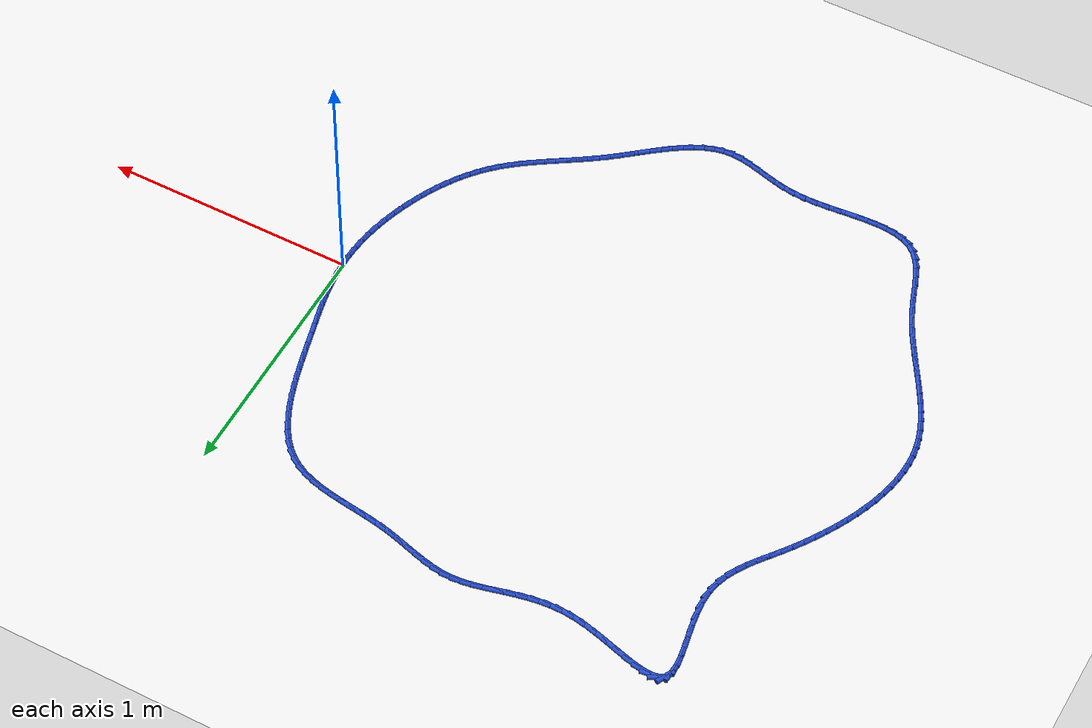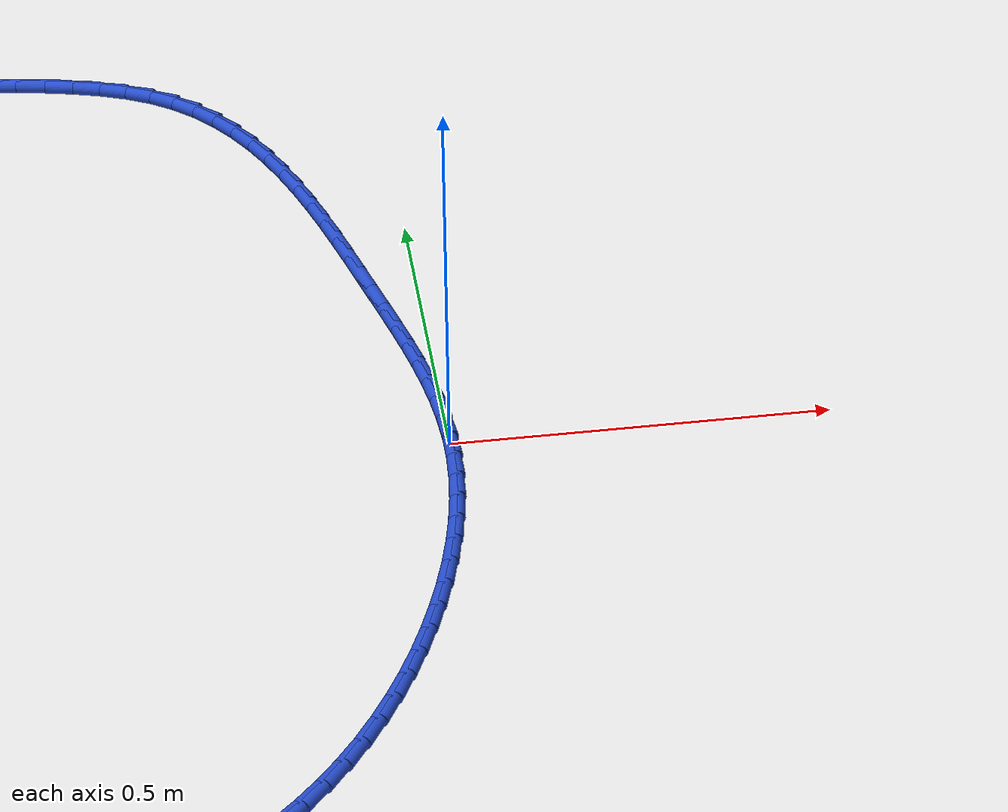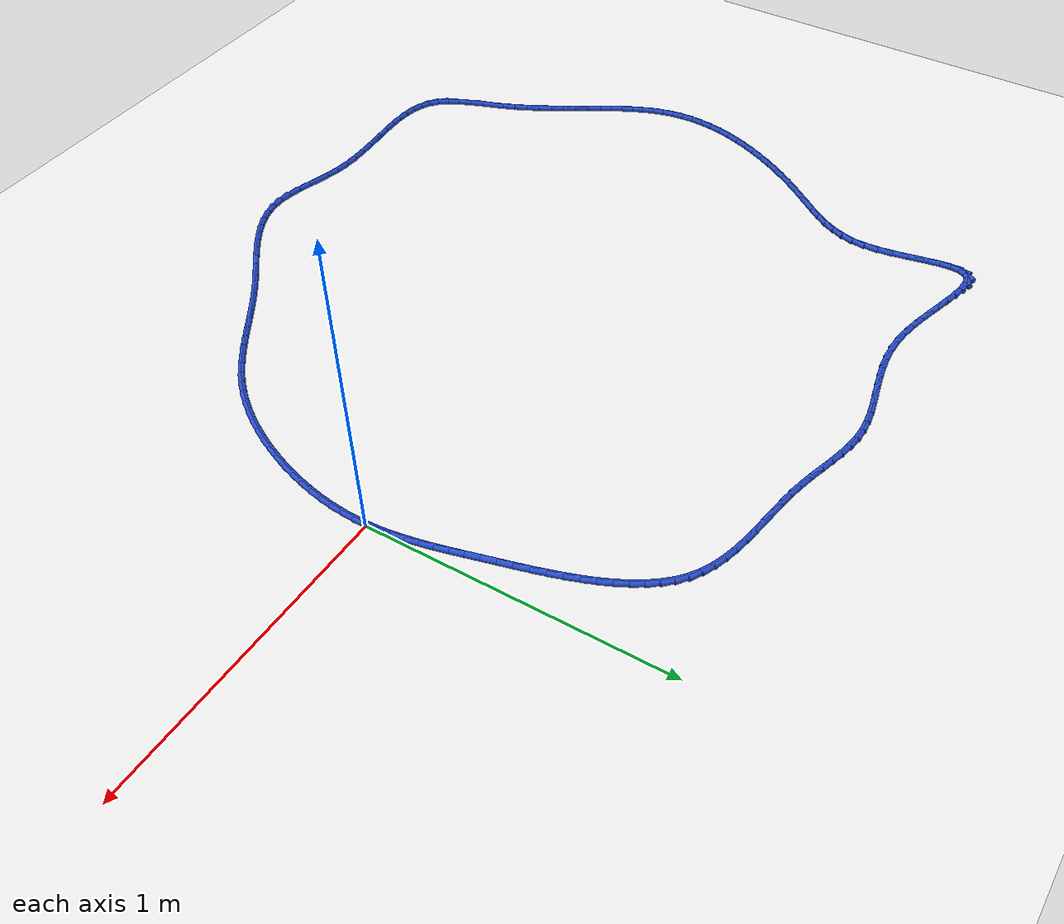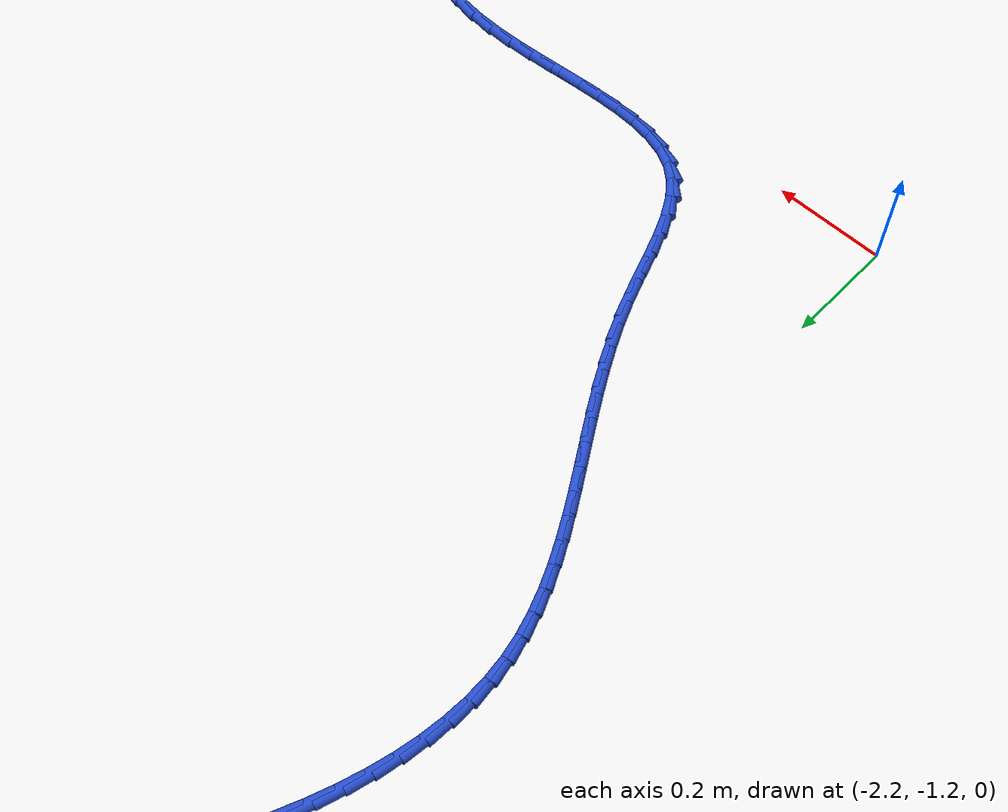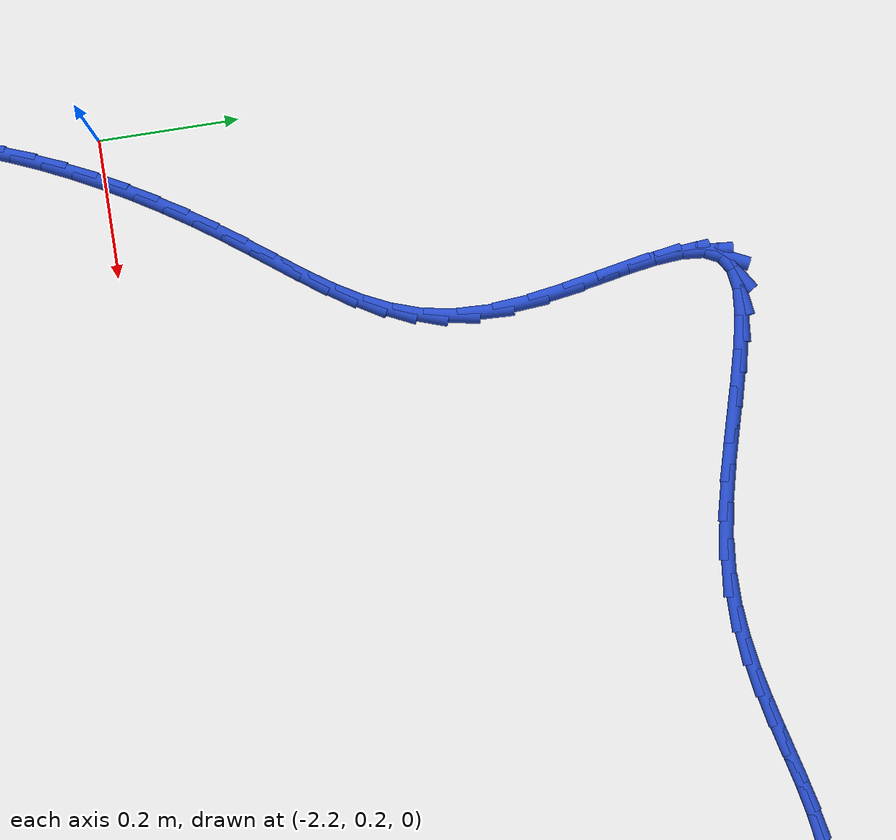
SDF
<sdf version="1.6">
 <world name="default">
  <light name="sun" type="directional">
   <pose>0 0 10 0 -0 0</pose>
   <diffuse>0.8 0.8 0.8 1</diffuse>
   <specular>0.2 0.2 0.2 1</specular>
   <attenuation>
    <range>1000</range>
    <constant>0.9</constant>
    <linear>0.01</linear>
    <quadratic>0.001</quadratic>
   </attenuation>
   <direction>-0.5 0.1 -0.9</direction>
  </light>
  <model name="ground_plane">
   <static>1</static>
   <link name="link">
    <collision name="collision">
     <geometry><plane><normal>0 0 1</normal><size>100 100</size></plane></geometry>
     <surface><friction><ode><mu>100</mu><mu2>50</mu2></ode></friction></surface>
    </collision>
    <visual name="visual">
     <cast_shadows>0</cast_shadows>
     <geometry><plane><normal>0 0 1</normal><size>100 100</size></plane></geometry>
     <material>
      <script><uri>file://media/materials/scripts/gazebo.material</uri><name>Gazebo/WhiteGlow</name></script>
     </material>
    </visual>
   </link>
  </model>
  <gravity>0 0 -9.8</gravity>
  <magnetic_field>6e-06 2.3e-05 -4.2e-05</magnetic_field>
  <atmosphere type="adiabatic"/>
  <physics name="default_physics" default="0" type="ode">
   <max_step_size>0.001</max_step_size>
   <real_time_factor>1</real_time_factor>
   <real_time_update_rate>1000</real_time_update_rate>
  </physics>
  <scene><ambient>0.4 0.4 0.4 1</ambient><background>0.7 0.7 0.7 1</background><shadows>1</shadows></scene>
  <spherical_coordinates>
   <surface_model>EARTH_WGS84</surface_model>
   <latitude_deg>0</latitude_deg>
   <longitude_deg>0</longitude_deg>
   <elevation>0</elevation>
   <heading_deg>0</heading_deg>
  </spherical_coordinates>
  <model name="line">
   <link name="link_0">
    <pose>-5.204170427930421e-18 -1.3877787807814457e-17 0.01 0 1.57 -1.5182289970396456</pose>
    <collision name="collision">
     <geometry><cylinder><radius>0.01</radius><length>0.08</length></cylinder></geometry>
    </collision>
    <visual name="visual">
     <material>
      <script><name>Gazebo/Blue</name><uri>file://media/materials/scripts/gazebo.material</uri></script>
     </material>
     <geometry><cylinder><radius>0.01</radius><length>0.08</length></cylinder></geometry>
    </visual>
   </link>
   <link name="link_1">
    <pose>-0.0022061180582929395 0.04192881055583981 0.01 0 1.57 -1.4680219667394454</pose>
    <collision name="collision">
     <geometry><cylinder><radius>0.01</radius><length>0.08</length></cylinder></geometry>
    </collision>
    <visual name="visual">
     <material>
      <script><name>Gazebo/Blue</name><uri>file://media/materials/scripts/gazebo.material</uri></script>
     </material>
     <geometry><cylinder><radius>0.01</radius><length>0.08</length></cylinder></geometry>
    </visual>
   </link>
   <link name="link_2">
    <pose>-0.006507748239843275 0.08363643181017488 0.01 0 1.57 -1.4246012355314652</pose>
    <collision name="collision">
     <geometry><cylinder><radius>0.01</radius><length>0.08</length></cylinder></geometry>
    </collision>
    <visual name="visual">
     <material>
      <script><name>Gazebo/Blue</name><uri>file://media/materials/scripts/gazebo.material</uri></script>
     </material>
     <geometry><cylinder><radius>0.01</radius><length>0.08</length></cylinder></geometry>
    </visual>
   </link>
   <link name="link_3">
    <pose>-0.012638954123299352 0.12527574199859687 0.01 0 1.57 -1.3884224651269705</pose>
    <collision name="collision">
     <geometry><cylinder><radius>0.01</radius><length>0.08</length></cylinder></geometry>
    </collision>
    <visual name="visual">
     <material>
      <script><name>Gazebo/Blue</name><uri>file://media/materials/scripts/gazebo.material</uri></script>
     </material>
     <geometry><cylinder><radius>0.01</radius><length>0.08</length></cylinder></geometry>
    </visual>
   </link>
   <link name="link_4">
    <pose>-0.02033379928730955 0.16699961935669771 0.01 0 1.57 -1.359683945157406</pose>
    <collision name="collision">
     <geometry><cylinder><radius>0.01</radius><length>0.08</length></cylinder></geometry>
    </collision>
    <visual name="visual">
     <material>
      <script><name>Gazebo/Blue</name><uri>file://media/materials/scripts/gazebo.material</uri></script>
     </material>
     <geometry><cylinder><radius>0.01</radius><length>0.08</length></cylinder></geometry>
    </visual>
   </link>
   <link name="link_5">
    <pose>-0.029326347310522242 0.20896094212006916 0.01 0 1.57 -1.3383811070145977</pose>
    <collision name="collision">
     <geometry><cylinder><radius>0.01</radius><length>0.08</length></cylinder></geometry>
    </collision>
    <visual name="visual">
     <material>
      <script><name>Gazebo/Blue</name><uri>file://media/materials/scripts/gazebo.material</uri></script>
     </material>
     <geometry><cylinder><radius>0.01</radius><length>0.08</length></cylinder></geometry>
    </visual>
   </link>
   <link name="link_6">
    <pose>-0.03935066177158577 0.251312588524303 0.01 0 1.57 -1.3243605703124162</pose>
    <collision name="collision">
     <geometry><cylinder><radius>0.01</radius><length>0.08</length></cylinder></geometry>
    </collision>
    <visual name="visual">
     <material>
      <script><name>Gazebo/Blue</name><uri>file://media/materials/scripts/gazebo.material</uri></script>
     </material>
     <geometry><cylinder><radius>0.01</radius><length>0.08</length></cylinder></geometry>
    </visual>
   </link>
   <link name="link_7">
    <pose>-0.050140806249148524 0.294207436804991 0.01 0 1.57 -1.3173654427160473</pose>
    <collision name="collision">
     <geometry><cylinder><radius>0.01</radius><length>0.08</length></cylinder></geometry>
    </collision>
    <visual name="visual">
     <material>
      <script><name>Gazebo/Blue</name><uri>file://media/materials/scripts/gazebo.material</uri></script>
     </material>
     <geometry><cylinder><radius>0.01</radius><length>0.08</length></cylinder></geometry>
    </visual>
   </link>
   <link name="link_8">
    <pose>-0.06143084432185886 0.3377983651977251 0.01 0 1.57 -1.3168349489651683</pose>
    <collision name="collision">
     <geometry><cylinder><radius>0.01</radius><length>0.08</length></cylinder></geometry>
    </collision>
    <visual name="visual">
     <material>
      <script><name>Gazebo/Blue</name><uri>file://media/materials/scripts/gazebo.material</uri></script>
     </material>
     <geometry><cylinder><radius>0.01</radius><length>0.08</length></cylinder></geometry>
    </visual>
   </link>
   <link name="link_9">
    <pose>-0.07296340628807133 0.3822285586163784 0.01 0 1.57 -1.3163146088564928</pose>
    <collision name="collision">
     <geometry><cylinder><radius>0.01</radius><length>0.08</length></cylinder></geometry>
    </collision>
    <visual name="visual">
     <material>
      <script><name>Gazebo/Blue</name><uri>file://media/materials/scripts/gazebo.material</uri></script>
     </material>
     <geometry><cylinder><radius>0.01</radius><length>0.08</length></cylinder></geometry>
    </visual>
   </link>
   <link name="link_10">
    <pose>-0.08470910282650652 0.42738324008880624 0.01 0 1.57 -1.3092367721181193</pose>
    <collision name="collision">
     <geometry><cylinder><radius>0.01</radius><length>0.08</length></cylinder></geometry>
    </collision>
    <visual name="visual">
     <material>
      <script><name>Gazebo/Blue</name><uri>file://media/materials/scripts/gazebo.material</uri></script>
     </material>
     <geometry><cylinder><radius>0.01</radius><length>0.08</length></cylinder></geometry>
    </visual>
   </link>
   <link name="link_11">
    <pose>-0.09688516991622112 0.47286857385933057 0.01 0 1.57 -1.295304637202215</pose>
    <collision name="collision">
     <geometry><cylinder><radius>0.01</radius><length>0.08</length></cylinder></geometry>
    </collision>
    <visual name="visual">
     <material>
      <script><name>Gazebo/Blue</name><uri>file://media/materials/scripts/gazebo.material</uri></script>
     </material>
     <geometry><cylinder><radius>0.01</radius><length>0.08</length></cylinder></geometry>
    </visual>
   </link>
   <link name="link_12">
    <pose>-0.10972114646521612 0.5182768032956219 0.01 0 1.57 -1.2742741325236298</pose>
    <collision name="collision">
     <geometry><cylinder><radius>0.01</radius><length>0.08</length></cylinder></geometry>
    </collision>
    <visual name="visual">
     <material>
      <script><name>Gazebo/Blue</name><uri>file://media/materials/scripts/gazebo.material</uri></script>
     </material>
     <geometry><cylinder><radius>0.01</radius><length>0.08</length></cylinder></geometry>
    </visual>
   </link>
   <link name="link_13">
    <pose>-0.1234465713814924 0.5632001717653504 0.01 0 1.57 -1.245626042232707</pose>
    <collision name="collision">
     <geometry><cylinder><radius>0.01</radius><length>0.08</length></cylinder></geometry>
    </collision>
    <visual name="visual">
     <material>
      <script><name>Gazebo/Blue</name><uri>file://media/materials/scripts/gazebo.material</uri></script>
     </material>
     <geometry><cylinder><radius>0.01</radius><length>0.08</length></cylinder></geometry>
    </visual>
   </link>
   <link name="link_14">
    <pose>-0.1382909835730509 0.6072309226361868 0.01 0 1.57 -1.208561783417686</pose>
    <collision name="collision">
     <geometry><cylinder><radius>0.01</radius><length>0.08</length></cylinder></geometry>
    </collision>
    <visual name="visual">
     <material>
      <script><name>Gazebo/Blue</name><uri>file://media/materials/scripts/gazebo.material</uri></script>
     </material>
     <geometry><cylinder><radius>0.01</radius><length>0.08</length></cylinder></geometry>
    </visual>
   </link>
   <link name="link_15">
    <pose>-0.15448392194789257 0.6499612992758016 0.01 0 1.57 -1.1619973383360662</pose>
    <collision name="collision">
     <geometry><cylinder><radius>0.01</radius><length>0.08</length></cylinder></geometry>
    </collision>
    <visual name="visual">
     <material>
      <script><name>Gazebo/Blue</name><uri>file://media/materials/scripts/gazebo.material</uri></script>
     </material>
     <geometry><cylinder><radius>0.01</radius><length>0.08</length></cylinder></geometry>
    </visual>
   </link>
   <link name="link_16">
    <pose>-0.17225492541401838 0.6909835450518651 0.01 0 1.57 -1.1045729637587336</pose>
    <collision name="collision">
     <geometry><cylinder><radius>0.01</radius><length>0.08</length></cylinder></geometry>
    </collision>
    <visual name="visual">
     <material>
      <script><name>Gazebo/Blue</name><uri>file://media/materials/scripts/gazebo.material</uri></script>
     </material>
     <geometry><cylinder><radius>0.01</radius><length>0.08</length></cylinder></geometry>
    </visual>
   </link>
   <link name="link_17">
    <pose>-0.19183353287942922 0.7298899033320482 0.01 0 1.57 -1.0347105124376785</pose>
    <collision name="collision">
     <geometry><cylinder><radius>0.01</radius><length>0.08</length></cylinder></geometry>
    </collision>
    <visual name="visual">
     <material>
      <script><name>Gazebo/Blue</name><uri>file://media/materials/scripts/gazebo.material</uri></script>
     </material>
     <geometry><cylinder><radius>0.01</radius><length>0.08</length></cylinder></geometry>
    </visual>
   </link>
   <link name="link_18">
    <pose>-0.2134492832521261 0.7662726174840209 0.01 0 1.57 -0.9507718071134559</pose>
    <collision name="collision">
     <geometry><cylinder><radius>0.01</radius><length>0.08</length></cylinder></geometry>
    </collision>
    <visual name="visual">
     <material>
      <script><name>Gazebo/Blue</name><uri>file://media/materials/scripts/gazebo.material</uri></script>
     </material>
     <geometry><cylinder><radius>0.01</radius><length>0.08</length></cylinder></geometry>
    </visual>
   </link>
   <link name="link_19">
    <pose>-0.23733171544010984 0.7997239308754538 0.01 0 1.57 -0.8513926401211741</pose>
    <collision name="collision">
     <geometry><cylinder><radius>0.01</radius><length>0.08</length></cylinder></geometry>
    </collision>
    <visual name="visual">
     <material>
      <script><name>Gazebo/Blue</name><uri>file://media/materials/scripts/gazebo.material</uri></script>
     </material>
     <geometry><cylinder><radius>0.01</radius><length>0.08</length></cylinder></geometry>
    </visual>
   </link>
   <link name="link_20">
    <pose>-0.2637103683513814 0.8298360868740172 0.01 0 1.57 -0.7360568193239986</pose>
    <collision name="collision">
     <geometry><cylinder><radius>0.01</radius><length>0.08</length></cylinder></geometry>
    </collision>
    <visual name="visual">
     <material>
      <script><name>Gazebo/Blue</name><uri>file://media/materials/scripts/gazebo.material</uri></script>
     </material>
     <geometry><cylinder><radius>0.01</radius><length>0.08</length></cylinder></geometry>
    </visual>
   </link>
   <link name="link_21">
    <pose>-0.2928147808939419 0.8562013288473824 0.01 0 1.57 -0.6059687174385548</pose>
    <collision name="collision">
     <geometry><cylinder><radius>0.01</radius><length>0.08</length></cylinder></geometry>
    </collision>
    <visual name="visual">
     <material>
      <script><name>Gazebo/Blue</name><uri>file://media/materials/scripts/gazebo.material</uri></script>
     </material>
     <geometry><cylinder><radius>0.01</radius><length>0.08</length></cylinder></geometry>
    </visual>
   </link>
   <link name="link_22">
    <pose>-0.3248725313810998 0.8784152717954565 0.01 0 1.57 -0.4747172335471271</pose>
    <collision name="collision">
     <geometry><cylinder><radius>0.01</radius><length>0.08</length></cylinder></geometry>
    </collision>
    <visual name="visual">
     <material>
      <script><name>Gazebo/Blue</name><uri>file://media/materials/scripts/gazebo.material</uri></script>
     </material>
     <geometry><cylinder><radius>0.01</radius><length>0.08</length></cylinder></geometry>
    </visual>
   </link>
   <link name="link_23">
    <pose>-0.35990910097877504 0.8964210769295646 0.01 0 1.57 -0.3648271021216497</pose>
    <collision name="collision">
     <geometry><cylinder><radius>0.01</radius><length>0.08</length></cylinder></geometry>
    </collision>
    <visual name="visual">
     <material>
      <script><name>Gazebo/Blue</name><uri>file://media/materials/scripts/gazebo.material</uri></script>
     </material>
     <geometry><cylinder><radius>0.01</radius><length>0.08</length></cylinder></geometry>
    </visual>
   </link>
   <link name="link_24">
    <pose>-0.3975750748693542 0.9108066136146813 0.01 0 1.57 -0.27880123905119975</pose>
    <collision name="collision">
     <geometry><cylinder><radius>0.01</radius><length>0.08</length></cylinder></geometry>
    </collision>
    <visual name="visual">
     <material>
      <script><name>Gazebo/Blue</name><uri>file://media/materials/scripts/gazebo.material</uri></script>
     </material>
     <geometry><cylinder><radius>0.01</radius><length>0.08</length></cylinder></geometry>
    </visual>
   </link>
   <link name="link_25">
    <pose>-0.43748032467524817 0.9222297662739143 0.01 0 1.57 -0.21501206148060215</pose>
    <collision name="collision">
     <geometry><cylinder><radius>0.01</radius><length>0.08</length></cylinder></geometry>
    </collision>
    <visual name="visual">
     <material>
      <script><name>Gazebo/Blue</name><uri>file://media/materials/scripts/gazebo.material</uri></script>
     </material>
     <geometry><cylinder><radius>0.01</radius><length>0.08</length></cylinder></geometry>
    </visual>
   </link>
   <link name="link_26">
    <pose>-0.4792347220188678 0.9313484193303705 0.01 0 1.57 -0.17121718909155448</pose>
    <collision name="collision">
     <geometry><cylinder><radius>0.01</radius><length>0.08</length></cylinder></geometry>
    </collision>
    <visual name="visual">
     <material>
      <script><name>Gazebo/Blue</name><uri>file://media/materials/scripts/gazebo.material</uri></script>
     </material>
     <geometry><cylinder><radius>0.01</radius><length>0.08</length></cylinder></geometry>
    </visual>
   </link>
   <link name="link_27">
    <pose>-0.5224481385226242 0.9388204572071572 0.01 0 1.57 -0.14537566169483054</pose>
    <collision name="collision">
     <geometry><cylinder><radius>0.01</radius><length>0.08</length></cylinder></geometry>
    </collision>
    <visual name="visual">
     <material>
      <script><name>Gazebo/Blue</name><uri>file://media/materials/scripts/gazebo.material</uri></script>
     </material>
     <geometry><cylinder><radius>0.01</radius><length>0.08</length></cylinder></geometry>
    </visual>
   </link>
   <link name="link_28">
    <pose>-0.5667304458089284 0.9453037643273818 0.01 0 1.57 -0.13599508970299026</pose>
    <collision name="collision">
     <geometry><cylinder><radius>0.01</radius><length>0.08</length></cylinder></geometry>
    </collision>
    <visual name="visual">
     <material>
      <script><name>Gazebo/Blue</name><uri>file://media/materials/scripts/gazebo.material</uri></script>
     </material>
     <geometry><cylinder><radius>0.01</radius><length>0.08</length></cylinder></geometry>
    </visual>
   </link>
   <link name="link_29">
    <pose>-0.6116915155001913 0.9514562251141516 0.01 0 1.57 -0.1422274362618129</pose>
    <collision name="collision">
     <geometry><cylinder><radius>0.01</radius><length>0.08</length></cylinder></geometry>
    </collision>
    <visual name="visual">
     <material>
      <script><name>Gazebo/Blue</name><uri>file://media/materials/scripts/gazebo.material</uri></script>
     </material>
     <geometry><cylinder><radius>0.01</radius><length>0.08</length></cylinder></geometry>
    </visual>
   </link>
   <link name="link_30">
    <pose>-0.6569412192188236 0.9579357239905739 0.01 0 1.57 -0.16384932030573837</pose>
    <collision name="collision">
     <geometry><cylinder><radius>0.01</radius><length>0.08</length></cylinder></geometry>
    </collision>
    <visual name="visual">
     <material>
      <script><name>Gazebo/Blue</name><uri>file://media/materials/scripts/gazebo.material</uri></script>
     </material>
     <geometry><cylinder><radius>0.01</radius><length>0.08</length></cylinder></geometry>
    </visual>
   </link>
   <link name="link_31">
    <pose>-0.702089428587237 0.9654001453797562 0.01 0 1.57 -0.20117469059565068</pose>
    <collision name="collision">
     <geometry><cylinder><radius>0.01</radius><length>0.08</length></cylinder></geometry>
    </collision>
    <visual name="visual">
     <material>
      <script><name>Gazebo/Blue</name><uri>file://media/materials/scripts/gazebo.material</uri></script>
     </material>
     <geometry><cylinder><radius>0.01</radius><length>0.08</length></cylinder></geometry>
    </visual>
   </link>
   <link name="link_32">
    <pose>-0.7467460814729165 0.9745071234151442 0.01 0 1.57 -0.24643039365060754</pose>
    <collision name="collision">
     <geometry><cylinder><radius>0.01</radius><length>0.08</length></cylinder></geometry>
    </collision>
    <visual name="visual">
     <material>
      <script><name>Gazebo/Blue</name><uri>file://media/materials/scripts/gazebo.material</uri></script>
     </material>
     <geometry><cylinder><radius>0.01</radius><length>0.08</length></cylinder></geometry>
    </visual>
   </link>
   <link name="link_33">
    <pose>-0.7906193504310315 0.9855431381958333 0.01 0 1.57 -0.2745067943539725</pose>
    <collision name="collision">
     <geometry><cylinder><radius>0.01</radius><length>0.08</length></cylinder></geometry>
    </collision>
    <visual name="visual">
     <material>
      <script><name>Gazebo/Blue</name><uri>file://media/materials/scripts/gazebo.material</uri></script>
     </material>
     <geometry><cylinder><radius>0.01</radius><length>0.08</length></cylinder></geometry>
    </visual>
   </link>
   <link name="link_34">
    <pose>-0.8337127152648784 0.9976789287410628 0.01 0 1.57 -0.28028764187250527</pose>
    <collision name="collision">
     <geometry><cylinder><radius>0.01</radius><length>0.08</length></cylinder></geometry>
    </collision>
    <visual name="visual">
     <material>
      <script><name>Gazebo/Blue</name><uri>file://media/materials/scripts/gazebo.material</uri></script>
     </material>
     <geometry><cylinder><radius>0.01</radius><length>0.08</length></cylinder></geometry>
    </visual>
   </link>
   <link name="link_35">
    <pose>-0.8760849190826946 1.0098764361488493 0.01 0 1.57 -0.26280711233090204</pose>
    <collision name="collision">
     <geometry><cylinder><radius>0.01</radius><length>0.08</length></cylinder></geometry>
    </collision>
    <visual name="visual">
     <material>
      <script><name>Gazebo/Blue</name><uri>file://media/materials/scripts/gazebo.material</uri></script>
     </material>
     <geometry><cylinder><radius>0.01</radius><length>0.08</length></cylinder></geometry>
    </visual>
   </link>
   <link name="link_36">
    <pose>-0.9177947049927172 1.0210976015172093 0.01 0 1.57 -0.22033915591999895</pose>
    <collision name="collision">
     <geometry><cylinder><radius>0.01</radius><length>0.08</length></cylinder></geometry>
    </collision>
    <visual name="visual">
     <material>
      <script><name>Gazebo/Blue</name><uri>file://media/materials/scripts/gazebo.material</uri></script>
     </material>
     <geometry><cylinder><radius>0.01</radius><length>0.08</length></cylinder></geometry>
    </visual>
   </link>
   <link name="link_37">
    <pose>-0.9589008161031842 1.0303043659441598 0.01 0 1.57 -0.1505804078906732</pose>
    <collision name="collision">
     <geometry><cylinder><radius>0.01</radius><length>0.08</length></cylinder></geometry>
    </collision>
    <visual name="visual">
     <material>
      <script><name>Gazebo/Blue</name><uri>file://media/materials/scripts/gazebo.material</uri></script>
     </material>
     <geometry><cylinder><radius>0.01</radius><length>0.08</length></cylinder></geometry>
    </visual>
   </link>
   <link name="link_38">
    <pose>-0.9994619955223315 1.0364586705277163 0.01 0 1.57 -0.05203244879713401</pose>
    <collision name="collision">
     <geometry><cylinder><radius>0.01</radius><length>0.08</length></cylinder></geometry>
    </collision>
    <visual name="visual">
     <material>
      <script><name>Gazebo/Blue</name><uri>file://media/materials/scripts/gazebo.material</uri></script>
     </material>
     <geometry><cylinder><radius>0.01</radius><length>0.08</length></cylinder></geometry>
    </visual>
   </link>
   <link name="link_39">
    <pose>-1.0395393336311038 1.038545876527806 0.01 0 1.57 0.0543418125721716</pose>
    <collision name="collision">
     <geometry><cylinder><radius>0.01</radius><length>0.08</length></cylinder></geometry>
    </collision>
    <visual name="visual">
     <material>
      <script><name>Gazebo/Blue</name><uri>file://media/materials/scripts/gazebo.material</uri></script>
     </material>
     <geometry><cylinder><radius>0.01</radius><length>0.08</length></cylinder></geometry>
    </visual>
   </link>
   <link name="link_40">
    <pose>-1.0792774042038664 1.0363843095998966 0.01 0 1.57 0.1391484082744587</pose>
    <collision name="collision">
     <geometry><cylinder><radius>0.01</radius><length>0.08</length></cylinder></geometry>
    </collision>
    <visual name="visual">
     <material>
      <script><name>Gazebo/Blue</name><uri>file://media/materials/scripts/gazebo.material</uri></script>
     </material>
     <geometry><cylinder><radius>0.01</radius><length>0.08</length></cylinder></geometry>
    </visual>
   </link>
   <link name="link_41">
    <pose>-1.1189249381145328 1.0308315338863847 0.01 0 1.57 0.19881181890761923</pose>
    <collision name="collision">
     <geometry><cylinder><radius>0.01</radius><length>0.08</length></cylinder></geometry>
    </collision>
    <visual name="visual">
     <material>
      <script><name>Gazebo/Blue</name><uri>file://media/materials/scripts/gazebo.material</uri></script>
     </material>
     <geometry><cylinder><radius>0.01</radius><length>0.08</length></cylinder></geometry>
    </visual>
   </link>
   <link name="link_42">
    <pose>-1.1587372118044492 1.022810422621665 0.01 0 1.57 0.23344811970610313</pose>
    <collision name="collision">
     <geometry><cylinder><radius>0.01</radius><length>0.08</length></cylinder></geometry>
    </collision>
    <visual name="visual">
     <material>
      <script><name>Gazebo/Blue</name><uri>file://media/materials/scripts/gazebo.material</uri></script>
     </material>
     <geometry><cylinder><radius>0.01</radius><length>0.08</length></cylinder></geometry>
    </visual>
   </link>
   <link name="link_43">
    <pose>-1.1989695017149629 1.0132438490401319 0.01 0 1.57 0.24411033773854265</pose>
    <collision name="collision">
     <geometry><cylinder><radius>0.01</radius><length>0.08</length></cylinder></geometry>
    </collision>
    <visual name="visual">
     <material>
      <script><name>Gazebo/Blue</name><uri>file://media/materials/scripts/gazebo.material</uri></script>
     </material>
     <geometry><cylinder><radius>0.01</radius><length>0.08</length></cylinder></geometry>
    </visual>
   </link>
   <link name="link_44">
    <pose>-1.239877084287421 1.00305468637618 0.01 0 1.57 0.23210068798596767</pose>
    <collision name="collision">
     <geometry><cylinder><radius>0.01</radius><length>0.08</length></cylinder></geometry>
    </collision>
    <visual name="visual">
     <material>
      <script><name>Gazebo/Blue</name><uri>file://media/materials/scripts/gazebo.material</uri></script>
     </material>
     <geometry><cylinder><radius>0.01</radius><length>0.08</length></cylinder></geometry>
    </visual>
   </link>
   <link name="link_45">
    <pose>-1.28171523596317 0.9931658078642038 0.01 0 1.57 0.19875672014599838</pose>
    <collision name="collision">
     <geometry><cylinder><radius>0.01</radius><length>0.08</length></cylinder></geometry>
    </collision>
    <visual name="visual">
     <material>
      <script><name>Gazebo/Blue</name><uri>file://media/materials/scripts/gazebo.material</uri></script>
     </material>
     <geometry><cylinder><radius>0.01</radius><length>0.08</length></cylinder></geometry>
    </visual>
   </link>
   <link name="link_46">
    <pose>-1.3247392331835572 0.9845000867385987 0.01 0 1.57 0.14558742378545486</pose>
    <collision name="collision">
     <geometry><cylinder><radius>0.01</radius><length>0.08</length></cylinder></geometry>
    </collision>
    <visual name="visual">
     <material>
      <script><name>Gazebo/Blue</name><uri>file://media/materials/scripts/gazebo.material</uri></script>
     </material>
     <geometry><cylinder><radius>0.01</radius><length>0.08</length></cylinder></geometry>
    </visual>
   </link>
   <link name="link_47">
    <pose>-1.3692043523899293 0.9779803962337583 0.01 0 1.57 0.07461583450697072</pose>
    <collision name="collision">
     <geometry><cylinder><radius>0.01</radius><length>0.08</length></cylinder></geometry>
    </collision>
    <visual name="visual">
     <material>
      <script><name>Gazebo/Blue</name><uri>file://media/materials/scripts/gazebo.material</uri></script>
     </material>
     <geometry><cylinder><radius>0.01</radius><length>0.08</length></cylinder></geometry>
    </visual>
   </link>
   <link name="link_48">
    <pose>-1.4153658700236331 0.9745296095840782 0.01 0 1.57 -0.011243644711374139</pose>
    <collision name="collision">
     <geometry><cylinder><radius>0.01</radius><length>0.08</length></cylinder></geometry>
    </collision>
    <visual name="visual">
     <material>
      <script><name>Gazebo/Blue</name><uri>file://media/materials/scripts/gazebo.material</uri></script>
     </material>
     <geometry><cylinder><radius>0.01</radius><length>0.08</length></cylinder></geometry>
    </visual>
   </link>
   <link name="link_49">
    <pose>-1.4634790625260155 0.9750706000239524 0.01 0 1.57 -0.10761558193277132</pose>
    <collision name="collision">
     <geometry><cylinder><radius>0.01</radius><length>0.08</length></cylinder></geometry>
    </collision>
    <visual name="visual">
     <material>
      <script><name>Gazebo/Blue</name><uri>file://media/materials/scripts/gazebo.material</uri></script>
     </material>
     <geometry><cylinder><radius>0.01</radius><length>0.08</length></cylinder></geometry>
    </visual>
   </link>
   <link name="link_50">
    <pose>-1.5137869908170367 0.9805055140046122 0.01 0 1.57 -0.19323684448059875</pose>
    <collision name="collision">
     <geometry><cylinder><radius>0.01</radius><length>0.08</length></cylinder></geometry>
    </collision>
    <visual name="visual">
     <material>
      <script><name>Gazebo/Blue</name><uri>file://media/materials/scripts/gazebo.material</uri></script>
     </material>
     <geometry><cylinder><radius>0.01</radius><length>0.08</length></cylinder></geometry>
    </visual>
   </link>
   <link name="link_51">
    <pose>-1.5659266324204444 0.990708121149609 0.01 0 1.57 -0.24817131483991978</pose>
    <collision name="collision">
     <geometry><cylinder><radius>0.01</radius><length>0.08</length></cylinder></geometry>
    </collision>
    <visual name="visual">
     <material>
      <script><name>Gazebo/Blue</name><uri>file://media/materials/scripts/gazebo.material</uri></script>
     </material>
     <geometry><cylinder><radius>0.01</radius><length>0.08</length></cylinder></geometry>
    </visual>
   </link>
   <link name="link_52">
    <pose>-1.6186620097401376 1.0040709975331081 0.01 0 1.57 -0.2771564924149752</pose>
    <collision name="collision">
     <geometry><cylinder><radius>0.01</radius><length>0.08</length></cylinder></geometry>
    </collision>
    <visual name="visual">
     <material>
      <script><name>Gazebo/Blue</name><uri>file://media/materials/scripts/gazebo.material</uri></script>
     </material>
     <geometry><cylinder><radius>0.01</radius><length>0.08</length></cylinder></geometry>
    </visual>
   </link>
   <link name="link_53">
    <pose>-1.6706893178236808 1.0188716326224314 0.01 0 1.57 -0.2824677940301614</pose>
    <collision name="collision">
     <geometry><cylinder><radius>0.01</radius><length>0.08</length></cylinder></geometry>
    </collision>
    <visual name="visual">
     <material>
      <script><name>Gazebo/Blue</name><uri>file://media/materials/scripts/gazebo.material</uri></script>
     </material>
     <geometry><cylinder><radius>0.01</radius><length>0.08</length></cylinder></geometry>
    </visual>
   </link>
   <link name="link_54">
    <pose>-1.7207047517186396 1.0333875158849004 0.01 0 1.57 -0.2617086677111485</pose>
    <collision name="collision">
     <geometry><cylinder><radius>0.01</radius><length>0.08</length></cylinder></geometry>
    </collision>
    <visual name="visual">
     <material>
      <script><name>Gazebo/Blue</name><uri>file://media/materials/scripts/gazebo.material</uri></script>
     </material>
     <geometry><cylinder><radius>0.01</radius><length>0.08</length></cylinder></geometry>
    </visual>
   </link>
   <link name="link_55">
    <pose>-1.767404506472582 1.0458961367878383 0.01 0 1.57 -0.20567152623822782</pose>
    <collision name="collision">
     <geometry><cylinder><radius>0.01</radius><length>0.08</length></cylinder></geometry>
    </collision>
    <visual name="visual">
     <material>
      <script><name>Gazebo/Blue</name><uri>file://media/materials/scripts/gazebo.material</uri></script>
     </material>
     <geometry><cylinder><radius>0.01</radius><length>0.08</length></cylinder></geometry>
    </visual>
   </link>
   <link name="link_56">
    <pose>-1.8094847771330724 1.0546749847985661 0.01 0 1.57 -0.09174510103921285</pose>
    <collision name="collision">
     <geometry><cylinder><radius>0.01</radius><length>0.08</length></cylinder></geometry>
    </collision>
    <visual name="visual">
     <material>
      <script><name>Gazebo/Blue</name><uri>file://media/materials/scripts/gazebo.material</uri></script>
     </material>
     <geometry><cylinder><radius>0.01</radius><length>0.08</length></cylinder></geometry>
    </visual>
   </link>
   <link name="link_57">
    <pose>-1.8456417587476779 1.0580015493844064 0.01 0 1.57 0.1322428347625958</pose>
    <collision name="collision">
     <geometry><cylinder><radius>0.01</radius><length>0.08</length></cylinder></geometry>
    </collision>
    <visual name="visual">
     <material>
      <script><name>Gazebo/Blue</name><uri>file://media/materials/scripts/gazebo.material</uri></script>
     </material>
     <geometry><cylinder><radius>0.01</radius><length>0.08</length></cylinder></geometry>
    </visual>
   </link>
   <link name="link_58">
    <pose>-1.8745716463639641 1.054153320012681 0.01 0 1.57 0.5584641466114703</pose>
    <collision name="collision">
     <geometry><cylinder><radius>0.01</radius><length>0.08</length></cylinder></geometry>
    </collision>
    <visual name="visual">
     <material>
      <script><name>Gazebo/Blue</name><uri>file://media/materials/scripts/gazebo.material</uri></script>
     </material>
     <geometry><cylinder><radius>0.01</radius><length>0.08</length></cylinder></geometry>
    </visual>
   </link>
   <link name="link_59">
    <pose>-1.8949706350294975 1.0414077861507123 0.01 0 1.57 1.1208592005511742</pose>
    <collision name="collision">
     <geometry><cylinder><radius>0.01</radius><length>0.08</length></cylinder></geometry>
    </collision>
    <visual name="visual">
     <material>
      <script><name>Gazebo/Blue</name><uri>file://media/materials/scripts/gazebo.material</uri></script>
     </material>
     <geometry><cylinder><radius>0.01</radius><length>0.08</length></cylinder></geometry>
    </visual>
   </link>
   <link name="link_60">
    <pose>-1.9060129282466856 1.0185448314815748 0.01 0 1.57 1.4759221124248132</pose>
    <collision name="collision">
     <geometry><cylinder><radius>0.01</radius><length>0.08</length></cylinder></geometry>
    </collision>
    <visual name="visual">
     <material>
      <script><name>Gazebo/Blue</name><uri>file://media/materials/scripts/gazebo.material</uri></script>
     </material>
     <geometry><cylinder><radius>0.01</radius><length>0.08</length></cylinder></geometry>
    </visual>
   </link>
   <link name="link_61">
    <pose>-1.9090497136467701 0.9866323833893106 0.01 0 1.57 -1.494545546196948</pose>
    <collision name="collision">
     <geometry><cylinder><radius>0.01</radius><length>0.08</length></cylinder></geometry>
    </collision>
    <visual name="visual">
     <material>
      <script><name>Gazebo/Blue</name><uri>file://media/materials/scripts/gazebo.material</uri></script>
     </material>
     <geometry><cylinder><radius>0.01</radius><length>0.08</length></cylinder></geometry>
    </visual>
   </link>
   <link name="link_62">
    <pose>-1.9060515913033171 0.9473893812328287 0.01 0 1.57 -1.4146276621818226</pose>
    <collision name="collision">
     <geometry><cylinder><radius>0.01</radius><length>0.08</length></cylinder></geometry>
    </collision>
    <visual name="visual">
     <material>
      <script><name>Gazebo/Blue</name><uri>file://media/materials/scripts/gazebo.material</uri></script>
     </material>
     <geometry><cylinder><radius>0.01</radius><length>0.08</length></cylinder></geometry>
    </visual>
   </link>
   <link name="link_63">
    <pose>-1.898989205321892 0.9025348106493424 0.01 0 1.57 -1.3851330176132328</pose>
    <collision name="collision">
     <geometry><cylinder><radius>0.01</radius><length>0.08</length></cylinder></geometry>
    </collision>
    <visual name="visual">
     <material>
      <script><name>Gazebo/Blue</name><uri>file://media/materials/scripts/gazebo.material</uri></script>
     </material>
     <geometry><cylinder><radius>0.01</radius><length>0.08</length></cylinder></geometry>
    </visual>
   </link>
   <link name="link_64">
    <pose>-1.8898331998080606 0.8537876572760671 0.01 0 1.57 -1.3905500592518238</pose>
    <collision name="collision">
     <geometry><cylinder><radius>0.01</radius><length>0.08</length></cylinder></geometry>
    </collision>
    <visual name="visual">
     <material>
      <script><name>Gazebo/Blue</name><uri>file://media/materials/scripts/gazebo.material</uri></script>
     </material>
     <geometry><cylinder><radius>0.01</radius><length>0.08</length></cylinder></geometry>
    </visual>
   </link>
   <link name="link_65">
    <pose>-1.8805542188673878 0.8028669067502168 0.01 0 1.57 -1.4271452669726987</pose>
    <collision name="collision">
     <geometry><cylinder><radius>0.01</radius><length>0.08</length></cylinder></geometry>
    </collision>
    <visual name="visual">
     <material>
      <script><name>Gazebo/Blue</name><uri>file://media/materials/scripts/gazebo.material</uri></script>
     </material>
     <geometry><cylinder><radius>0.01</radius><length>0.08</length></cylinder></geometry>
    </visual>
   </link>
   <link name="link_66">
    <pose>-1.87312290660544 0.7514915447090058 0.01 0 1.57 -1.4988209282986549</pose>
    <collision name="collision">
     <geometry><cylinder><radius>0.01</radius><length>0.08</length></cylinder></geometry>
    </collision>
    <visual name="visual">
     <material>
      <script><name>Gazebo/Blue</name><uri>file://media/materials/scripts/gazebo.material</uri></script>
     </material>
     <geometry><cylinder><radius>0.01</radius><length>0.08</length></cylinder></geometry>
    </visual>
   </link>
   <link name="link_67">
    <pose>-1.8695099071277803 0.7013805567896486 0.01 0 1.57 1.5257412523440472</pose>
    <collision name="collision">
     <geometry><cylinder><radius>0.01</radius><length>0.08</length></cylinder></geometry>
    </collision>
    <visual name="visual">
     <material>
      <script><name>Gazebo/Blue</name><uri>file://media/materials/scripts/gazebo.material</uri></script>
     </material>
     <geometry><cylinder><radius>0.01</radius><length>0.08</length></cylinder></geometry>
    </visual>
   </link>
   <link name="link_68">
    <pose>-1.8716364919369075 0.654212825302235 0.01 0 1.57 1.379378935516217</pose>
    <collision name="collision">
     <geometry><cylinder><radius>0.01</radius><length>0.08</length></cylinder></geometry>
    </collision>
    <visual name="visual">
     <material>
      <script><name>Gazebo/Blue</name><uri>file://media/materials/scripts/gazebo.material</uri></script>
     </material>
     <geometry><cylinder><radius>0.01</radius><length>0.08</length></cylinder></geometry>
    </visual>
   </link>
   <link name="link_69">
    <pose>-1.8800911887932432 0.6105846998375098 0.01 0 1.57 1.2410665539385004</pose>
    <collision name="collision">
     <geometry><cylinder><radius>0.01</radius><length>0.08</length></cylinder></geometry>
    </collision>
    <visual name="visual">
     <material>
      <script><name>Gazebo/Blue</name><uri>file://media/materials/scripts/gazebo.material</uri></script>
     </material>
     <geometry><cylinder><radius>0.01</radius><length>0.08</length></cylinder></geometry>
    </visual>
   </link>
   <link name="link_70">
    <pose>-1.8940100625512886 0.5699127543326853 0.01 0 1.57 1.1225662686337843</pose>
    <collision name="collision">
     <geometry><cylinder><radius>0.01</radius><length>0.08</length></cylinder></geometry>
    </collision>
    <visual name="visual">
     <material>
      <script><name>Gazebo/Blue</name><uri>file://media/materials/scripts/gazebo.material</uri></script>
     </material>
     <geometry><cylinder><radius>0.01</radius><length>0.08</length></cylinder></geometry>
    </visual>
   </link>
   <link name="link_71">
    <pose>-1.9124558060752903 0.5315539656864534 0.01 0 1.57 1.02993376319213</pose>
    <collision name="collision">
     <geometry><cylinder><radius>0.01</radius><length>0.08</length></cylinder></geometry>
    </collision>
    <visual name="visual">
     <material>
      <script><name>Gazebo/Blue</name><uri>file://media/materials/scripts/gazebo.material</uri></script>
     </material>
     <geometry><cylinder><radius>0.01</radius><length>0.08</length></cylinder></geometry>
    </visual>
   </link>
   <link name="link_72">
    <pose>-1.9344911122294954 0.4948653107975075 0.01 0 1.57 0.9652744058760457</pose>
    <collision name="collision">
     <geometry><cylinder><radius>0.01</radius><length>0.08</length></cylinder></geometry>
    </collision>
    <visual name="visual">
     <material>
      <script><name>Gazebo/Blue</name><uri>file://media/materials/scripts/gazebo.material</uri></script>
     </material>
     <geometry><cylinder><radius>0.01</radius><length>0.08</length></cylinder></geometry>
    </visual>
   </link>
   <link name="link_73">
    <pose>-1.9591786738781511 0.4592037665645399 0.01 0 1.57 0.9283043528845709</pose>
    <collision name="collision">
     <geometry><cylinder><radius>0.01</radius><length>0.08</length></cylinder></geometry>
    </collision>
    <visual name="visual">
     <material>
      <script><name>Gazebo/Blue</name><uri>file://media/materials/scripts/gazebo.material</uri></script>
     </material>
     <geometry><cylinder><radius>0.01</radius><length>0.08</length></cylinder></geometry>
    </visual>
   </link>
   <link name="link_74">
    <pose>-1.9855811838855058 0.42392630988624275 0.01 0 1.57 0.9178562485198895</pose>
    <collision name="collision">
     <geometry><cylinder><radius>0.01</radius><length>0.08</length></cylinder></geometry>
    </collision>
    <visual name="visual">
     <material>
      <script><name>Gazebo/Blue</name><uri>file://media/materials/scripts/gazebo.material</uri></script>
     </material>
     <geometry><cylinder><radius>0.01</radius><length>0.08</length></cylinder></geometry>
    </visual>
   </link>
   <link name="link_75">
    <pose>-2.012761335115804 0.38838991766130915 0.01 0 1.57 0.9322652607225258</pose>
    <collision name="collision">
     <geometry><cylinder><radius>0.01</radius><length>0.08</length></cylinder></geometry>
    </collision>
    <visual name="visual">
     <material>
      <script><name>Gazebo/Blue</name><uri>file://media/materials/scripts/gazebo.material</uri></script>
     </material>
     <geometry><cylinder><radius>0.01</radius><length>0.08</length></cylinder></geometry>
    </visual>
   </link>
   <link name="link_76">
    <pose>-2.0397966386434567 0.35196711272180276 0.01 0 1.57 0.9596612847192497</pose>
    <collision name="collision">
     <geometry><cylinder><radius>0.01</radius><length>0.08</length></cylinder></geometry>
    </collision>
    <visual name="visual">
     <material>
      <script><name>Gazebo/Blue</name><uri>file://media/materials/scripts/gazebo.material</uri></script>
     </material>
     <geometry><cylinder><radius>0.01</radius><length>0.08</length></cylinder></geometry>
    </visual>
   </link>
   <link name="link_77">
    <pose>-2.066116676792783 0.3143997793903388 0.01 0 1.57 0.9888542077969338</pose>
    <collision name="collision">
     <geometry><cylinder><radius>0.01</radius><length>0.08</length></cylinder></geometry>
    </collision>
    <visual name="visual">
     <material>
      <script><name>Gazebo/Blue</name><uri>file://media/materials/scripts/gazebo.material</uri></script>
     </material>
     <geometry><cylinder><radius>0.01</radius><length>0.08</length></cylinder></geometry>
    </visual>
   </link>
   <link name="link_78">
    <pose>-2.0915094703210313 0.27580584335585245 0.01 0 1.57 1.0196788205273468</pose>
    <collision name="collision">
     <geometry><cylinder><radius>0.01</radius><length>0.08</length></cylinder></geometry>
    </collision>
    <visual name="visual">
     <material>
      <script><name>Gazebo/Blue</name><uri>file://media/materials/scripts/gazebo.material</uri></script>
     </material>
     <geometry><cylinder><radius>0.01</radius><length>0.08</length></cylinder></geometry>
    </visual>
   </link>
   <link name="link_79">
    <pose>-2.115779131760458 0.23632011235034275 0.01 0 1.57 1.0524972764604403</pose>
    <collision name="collision">
     <geometry><cylinder><radius>0.01</radius><length>0.08</length></cylinder></geometry>
    </collision>
    <visual name="visual">
     <material>
      <script><name>Gazebo/Blue</name><uri>file://media/materials/scripts/gazebo.material</uri></script>
     </material>
     <geometry><cylinder><radius>0.01</radius><length>0.08</length></cylinder></geometry>
    </visual>
   </link>
   <link name="link_80">
    <pose>-2.1387297736433197 0.19607739410580985 0.01 0 1.57 1.0877011466438027</pose>
    <collision name="collision">
     <geometry><cylinder><radius>0.01</radius><length>0.08</length></cylinder></geometry>
    </collision>
    <visual name="visual">
     <material>
      <script><name>Gazebo/Blue</name><uri>file://media/materials/scripts/gazebo.material</uri></script>
     </material>
     <geometry><cylinder><radius>0.01</radius><length>0.08</length></cylinder></geometry>
    </visual>
   </link>
   <link name="link_81">
    <pose>-2.160165508501873 0.155212496354253 0.01 0 1.57 1.1257192514959045</pose>
    <collision name="collision">
     <geometry><cylinder><radius>0.01</radius><length>0.08</length></cylinder></geometry>
    </collision>
    <visual name="visual">
     <material>
      <script><name>Gazebo/Blue</name><uri>file://media/materials/scripts/gazebo.material</uri></script>
     </material>
     <geometry><cylinder><radius>0.01</radius><length>0.08</length></cylinder></geometry>
    </visual>
   </link>
   <link name="link_82">
    <pose>-2.1798904488683752 0.11386022682767119 0.01 0 1.57 1.1670241249108855</pose>
    <collision name="collision">
     <geometry><cylinder><radius>0.01</radius><length>0.08</length></cylinder></geometry>
    </collision>
    <visual name="visual">
     <material>
      <script><name>Gazebo/Blue</name><uri>file://media/materials/scripts/gazebo.material</uri></script>
     </material>
     <geometry><cylinder><radius>0.01</radius><length>0.08</length></cylinder></geometry>
    </visual>
   </link>
   <link name="link_83">
    <pose>-2.197708707275083 0.07215539325806489 0.01 0 1.57 1.2121361264298163</pose>
    <collision name="collision">
     <geometry><cylinder><radius>0.01</radius><length>0.08</length></cylinder></geometry>
    </collision>
    <visual name="visual">
     <material>
      <script><name>Gazebo/Blue</name><uri>file://media/materials/scripts/gazebo.material</uri></script>
     </material>
     <geometry><cylinder><radius>0.01</radius><length>0.08</length></cylinder></geometry>
    </visual>
   </link>
   <link name="link_84">
    <pose>-2.213424396254253 0.030232803377432785 0.01 0 1.57 1.2616234194661422</pose>
    <collision name="collision">
     <geometry><cylinder><radius>0.01</radius><length>0.08</length></cylinder></geometry>
    </collision>
    <visual name="visual">
     <material>
      <script><name>Gazebo/Blue</name><uri>file://media/materials/scripts/gazebo.material</uri></script>
     </material>
     <geometry><cylinder><radius>0.01</radius><length>0.08</length></cylinder></geometry>
    </visual>
   </link>
   <link name="link_85">
    <pose>-2.226841628338141 -0.011772735082224761 0.01 0 1.57 1.3160949373520707</pose>
    <collision name="collision">
     <geometry><cylinder><radius>0.01</radius><length>0.08</length></cylinder></geometry>
    </collision>
    <visual name="visual">
     <material>
      <script><name>Gazebo/Blue</name><uri>file://media/materials/scripts/gazebo.material</uri></script>
     </material>
     <geometry><cylinder><radius>0.01</radius><length>0.08</length></cylinder></geometry>
    </visual>
   </link>
   <link name="link_86">
    <pose>-2.2377645160590043 -0.05372641438890864 0.01 0 1.57 1.3761820714155157</pose>
    <collision name="collision">
     <geometry><cylinder><radius>0.01</radius><length>0.08</length></cylinder></geometry>
    </collision>
    <visual name="visual">
     <material>
      <script><name>Gazebo/Blue</name><uri>file://media/materials/scripts/gazebo.material</uri></script>
     </material>
     <geometry><cylinder><radius>0.01</radius><length>0.08</length></cylinder></geometry>
    </visual>
   </link>
   <link name="link_87">
    <pose>-2.2459971719491008 -0.09549342681061923 0.01 0 1.57 1.4425033524744262</pose>
    <collision name="collision">
     <geometry><cylinder><radius>0.01</radius><length>0.08</length></cylinder></geometry>
    </collision>
    <visual name="visual">
     <material>
      <script><name>Gazebo/Blue</name><uri>file://media/materials/scripts/gazebo.material</uri></script>
     </material>
     <geometry><cylinder><radius>0.01</radius><length>0.08</length></cylinder></geometry>
    </visual>
   </link>
   <link name="link_88">
    <pose>-2.2513437085406864 -0.1369389646153571 0.01 0 1.57 1.515605519801401</pose>
    <collision name="collision">
     <geometry><cylinder><radius>0.01</radius><length>0.08</length></cylinder></geometry>
    </collision>
    <visual name="visual">
     <material>
      <script><name>Gazebo/Blue</name><uri>file://media/materials/scripts/gazebo.material</uri></script>
     </material>
     <geometry><cylinder><radius>0.01</radius><length>0.08</length></cylinder></geometry>
    </visual>
   </link>
   <link name="link_89">
    <pose>-2.253608238366018 -0.1779282200711234 0.01 0 1.57 -1.5457171695179224</pose>
    <collision name="collision">
     <geometry><cylinder><radius>0.01</radius><length>0.08</length></cylinder></geometry>
    </collision>
    <visual name="visual">
     <material>
      <script><name>Gazebo/Blue</name><uri>file://media/materials/scripts/gazebo.material</uri></script>
     </material>
     <geometry><cylinder><radius>0.01</radius><length>0.08</length></cylinder></geometry>
    </visual>
   </link>
   <link name="link_90">
    <pose>-2.252594873957352 -0.2183263854459171 0.01 0 1.57 -1.4581852434171996</pose>
    <collision name="collision">
     <geometry><cylinder><radius>0.01</radius><length>0.08</length></cylinder></geometry>
    </collision>
    <visual name="visual">
     <material>
      <script><name>Gazebo/Blue</name><uri>file://media/materials/scripts/gazebo.material</uri></script>
     </material>
     <geometry><cylinder><radius>0.01</radius><length>0.08</length></cylinder></geometry>
    </visual>
   </link>
   <link name="link_91">
    <pose>-2.2481083224650704 -0.2579989493656181 0.01 0 1.57 -1.3679502620252153</pose>
    <collision name="collision">
     <geometry><cylinder><radius>0.01</radius><length>0.08</length></cylinder></geometry>
    </collision>
    <visual name="visual">
     <material>
      <script><name>Gazebo/Blue</name><uri>file://media/materials/scripts/gazebo.material</uri></script>
     </material>
     <geometry><cylinder><radius>0.01</radius><length>0.08</length></cylinder></geometry>
    </visual>
   </link>
   <link name="link_92">
    <pose>-2.2401095615766837 -0.2968892857458129 0.01 0 1.57 -1.286187726089869</pose>
    <collision name="collision">
     <geometry><cylinder><radius>0.01</radius><length>0.08</length></cylinder></geometry>
    </collision>
    <visual name="visual">
     <material>
      <script><name>Gazebo/Blue</name><uri>file://media/materials/scripts/gazebo.material</uri></script>
     </material>
     <geometry><cylinder><radius>0.01</radius><length>0.08</length></cylinder></geometry>
    </visual>
   </link>
   <link name="link_93">
    <pose>-2.228924382775723 -0.3351225918240899 0.01 0 1.57 -1.2156073930035167</pose>
    <collision name="collision">
     <geometry><cylinder><radius>0.01</radius><length>0.08</length></cylinder></geometry>
    </collision>
    <visual name="visual">
     <material>
      <script><name>Gazebo/Blue</name><uri>file://media/materials/scripts/gazebo.material</uri></script>
     </material>
     <geometry><cylinder><radius>0.01</radius><length>0.08</length></cylinder></geometry>
    </visual>
   </link>
   <link name="link_94">
    <pose>-2.2149305438873 -0.37284996488063965 0.01 0 1.57 -1.1567193964823947</pose>
    <collision name="collision">
     <geometry><cylinder><radius>0.01</radius><length>0.08</length></cylinder></geometry>
    </collision>
    <visual name="visual">
     <material>
      <script><name>Gazebo/Blue</name><uri>file://media/materials/scripts/gazebo.material</uri></script>
     </material>
     <geometry><cylinder><radius>0.01</radius><length>0.08</length></cylinder></geometry>
    </visual>
   </link>
   <link name="link_95">
    <pose>-2.198505802736524 -0.41022250219565054 0.01 0 1.57 -1.1094438876946617</pose>
    <collision name="collision">
     <geometry><cylinder><radius>0.01</radius><length>0.08</length></cylinder></geometry>
    </collision>
    <visual name="visual">
     <material>
      <script><name>Gazebo/Blue</name><uri>file://media/materials/scripts/gazebo.material</uri></script>
     </material>
     <geometry><cylinder><radius>0.01</radius><length>0.08</length></cylinder></geometry>
    </visual>
   </link>
   <link name="link_96">
    <pose>-2.1800279171485073 -0.44739130104931296 0.01 0 1.57 -1.0733599521147652</pose>
    <collision name="collision">
     <geometry><cylinder><radius>0.01</radius><length>0.08</length></cylinder></geometry>
    </collision>
    <visual name="visual">
     <material>
      <script><name>Gazebo/Blue</name><uri>file://media/materials/scripts/gazebo.material</uri></script>
     </material>
     <geometry><cylinder><radius>0.01</radius><length>0.08</length></cylinder></geometry>
    </visual>
   </link>
   <link name="link_97">
    <pose>-2.1598746449483595 -0.48450745872181683 0.01 0 1.57 -1.0479025266251936</pose>
    <collision name="collision">
     <geometry><cylinder><radius>0.01</radius><length>0.08</length></cylinder></geometry>
    </collision>
    <visual name="visual">
     <material>
      <script><name>Gazebo/Blue</name><uri>file://media/materials/scripts/gazebo.material</uri></script>
     </material>
     <geometry><cylinder><radius>0.01</radius><length>0.08</length></cylinder></geometry>
    </visual>
   </link>
   <link name="link_98">
    <pose>-2.1384237439611917 -0.5217220724933519 0.01 0 1.57 -1.0324938497927232</pose>
    <collision name="collision">
     <geometry><cylinder><radius>0.01</radius><length>0.08</length></cylinder></geometry>
    </collision>
    <visual name="visual">
     <material>
      <script><name>Gazebo/Blue</name><uri>file://media/materials/scripts/gazebo.material</uri></script>
     </material>
     <geometry><cylinder><radius>0.01</radius><length>0.08</length></cylinder></geometry>
    </visual>
   </link>
   <link name="link_99">
    <pose>-2.116052972012115 -0.5591862396441087 0.01 0 1.57 -1.0266181769225484</pose>
    <collision name="collision">
     <geometry><cylinder><radius>0.01</radius><length>0.08</length></cylinder></geometry>
    </collision>
    <visual name="visual">
     <material>
      <script><name>Gazebo/Blue</name><uri>file://media/materials/scripts/gazebo.material</uri></script>
     </material>
     <geometry><cylinder><radius>0.01</radius><length>0.08</length></cylinder></geometry>
    </visual>
   </link>
   <link name="link_100">
    <pose>-2.0931400869262404 -0.5970510574542758 0.01 0 1.57 -1.0298544494652497</pose>
    <collision name="collision">
     <geometry><cylinder><radius>0.01</radius><length>0.08</length></cylinder></geometry>
    </collision>
    <visual name="visual">
     <material>
      <script><name>Gazebo/Blue</name><uri>file://media/materials/scripts/gazebo.material</uri></script>
     </material>
     <geometry><cylinder><radius>0.01</radius><length>0.08</length></cylinder></geometry>
    </visual>
   </link>
   <link name="link_101">
    <pose>-2.070062846528679 -0.6354676232040435 0.01 0 1.57 -1.041879631007983</pose>
    <collision name="collision">
     <geometry><cylinder><radius>0.01</radius><length>0.08</length></cylinder></geometry>
    </collision>
    <visual name="visual">
     <material>
      <script><name>Gazebo/Blue</name><uri>file://media/materials/scripts/gazebo.material</uri></script>
     </material>
     <geometry><cylinder><radius>0.01</radius><length>0.08</length></cylinder></geometry>
    </visual>
   </link>
   <link name="link_102">
    <pose>-2.0471990086445397 -0.6745870341736014 0.01 0 1.57 -1.0624511637822287</pose>
    <collision name="collision">
     <geometry><cylinder><radius>0.01</radius><length>0.08</length></cylinder></geometry>
    </collision>
    <visual name="visual">
     <material>
      <script><name>Gazebo/Blue</name><uri>file://media/materials/scripts/gazebo.material</uri></script>
     </material>
     <geometry><cylinder><radius>0.01</radius><length>0.08</length></cylinder></geometry>
    </visual>
   </link>
   <link name="link_103">
    <pose>-2.0249263310989356 -0.7145603876431398 0.01 0 1.57 -1.091373182689228</pose>
    <collision name="collision">
     <geometry><cylinder><radius>0.01</radius><length>0.08</length></cylinder></geometry>
    </collision>
    <visual name="visual">
     <material>
      <script><name>Gazebo/Blue</name><uri>file://media/materials/scripts/gazebo.material</uri></script>
     </material>
     <geometry><cylinder><radius>0.01</radius><length>0.08</length></cylinder></geometry>
    </visual>
   </link>
   <link name="link_104">
    <pose>-2.003622571716976 -0.7555387808928489 0.01 0 1.57 -1.128448821963375</pose>
    <collision name="collision">
     <geometry><cylinder><radius>0.01</radius><length>0.08</length></cylinder></geometry>
    </collision>
    <visual name="visual">
     <material>
      <script><name>Gazebo/Blue</name><uri>file://media/materials/scripts/gazebo.material</uri></script>
     </material>
     <geometry><cylinder><radius>0.01</radius><length>0.08</length></cylinder></geometry>
    </visual>
   </link>
   <link name="link_105">
    <pose>-1.9836654883237737 -0.7976733112029174 0.01 0 1.57 -1.1733625011910476</pose>
    <collision name="collision">
     <geometry><cylinder><radius>0.01</radius><length>0.08</length></cylinder></geometry>
    </collision>
    <visual name="visual">
     <material>
      <script><name>Gazebo/Blue</name><uri>file://media/materials/scripts/gazebo.material</uri></script>
     </material>
     <geometry><cylinder><radius>0.01</radius><length>0.08</length></cylinder></geometry>
    </visual>
   </link>
   <link name="link_106">
    <pose>-1.9654307818061143 -0.8411129017752083 0.01 0 1.57 -1.2146667010125252</pose>
    <collision name="collision">
     <geometry><cylinder><radius>0.01</radius><length>0.08</length></cylinder></geometry>
    </collision>
    <visual name="visual">
     <material>
      <script><name>Gazebo/Blue</name><uri>file://media/materials/scripts/gazebo.material</uri></script>
     </material>
     <geometry><cylinder><radius>0.01</radius><length>0.08</length></cylinder></geometry>
    </visual>
   </link>
   <link name="link_107">
    <pose>-1.9488897847727067 -0.8855790792777132 0.01 0 1.57 -1.2287749456263017</pose>
    <collision name="collision">
     <geometry><cylinder><radius>0.01</radius><length>0.08</length></cylinder></geometry>
    </collision>
    <visual name="visual">
     <material>
      <script><name>Gazebo/Blue</name><uri>file://media/materials/scripts/gazebo.material</uri></script>
     </material>
     <geometry><cylinder><radius>0.01</radius><length>0.08</length></cylinder></geometry>
    </visual>
   </link>
   <link name="link_108">
    <pose>-1.933126723956542 -0.9298557449587018 0.01 0 1.57 -1.2122586625435408</pose>
    <collision name="collision">
     <geometry><cylinder><radius>0.01</radius><length>0.08</length></cylinder></geometry>
    </collision>
    <visual name="visual">
     <material>
      <script><name>Gazebo/Blue</name><uri>file://media/materials/scripts/gazebo.material</uri></script>
     </material>
     <geometry><cylinder><radius>0.01</radius><length>0.08</length></cylinder></geometry>
    </visual>
   </link>
   <link name="link_109">
    <pose>-1.9171080997069943 -0.9726023693159841 0.01 0 1.57 -1.1612961282283414</pose>
    <collision name="collision">
     <geometry><cylinder><radius>0.01</radius><length>0.08</length></cylinder></geometry>
    </collision>
    <visual name="visual">
     <material>
      <script><name>Gazebo/Blue</name><uri>file://media/materials/scripts/gazebo.material</uri></script>
     </material>
     <geometry><cylinder><radius>0.01</radius><length>0.08</length></cylinder></geometry>
    </visual>
   </link>
   <link name="link_110">
    <pose>-1.8998004123734344 -1.0124784228473693 0.01 0 1.57 -1.0676404747008688</pose>
    <collision name="collision">
     <geometry><cylinder><radius>0.01</radius><length>0.08</length></cylinder></geometry>
    </collision>
    <visual name="visual">
     <material>
      <script><name>Gazebo/Blue</name><uri>file://media/materials/scripts/gazebo.material</uri></script>
     </material>
     <geometry><cylinder><radius>0.01</radius><length>0.08</length></cylinder></geometry>
    </visual>
   </link>
   <link name="link_111">
    <pose>-1.8801701623052367 -1.0481433760506662 0.01 0 1.57 -0.9188203626276851</pose>
    <collision name="collision">
     <geometry><cylinder><radius>0.01</radius><length>0.08</length></cylinder></geometry>
    </collision>
    <visual name="visual">
     <material>
      <script><name>Gazebo/Blue</name><uri>file://media/materials/scripts/gazebo.material</uri></script>
     </material>
     <geometry><cylinder><radius>0.01</radius><length>0.08</length></cylinder></geometry>
    </visual>
   </link>
   <link name="link_112">
    <pose>-1.8571838498517723 -1.0782566994236835 0.01 0 1.57 -0.7071053586595186</pose>
    <collision name="collision">
     <geometry><cylinder><radius>0.01</radius><length>0.08</length></cylinder></geometry>
    </collision>
    <visual name="visual">
     <material>
      <script><name>Gazebo/Blue</name><uri>file://media/materials/scripts/gazebo.material</uri></script>
     </material>
     <geometry><cylinder><radius>0.01</radius><length>0.08</length></cylinder></geometry>
    </visual>
   </link>
   <link name="link_113">
    <pose>-1.8298813531937685 -1.1015869004399588 0.01 0 1.57 -0.4828977541649808</pose>
    <collision name="collision">
     <geometry><cylinder><radius>0.01</radius><length>0.08</length></cylinder></geometry>
    </collision>
    <visual name="visual">
     <material>
      <script><name>Gazebo/Blue</name><uri>file://media/materials/scripts/gazebo.material</uri></script>
     </material>
     <geometry><cylinder><radius>0.01</radius><length>0.08</length></cylinder></geometry>
    </visual>
   </link>
   <link name="link_114">
    <pose>-1.7981807757152024 -1.1182074995231877 0.01 0 1.57 -0.2956793770958877</pose>
    <collision name="collision">
     <geometry><cylinder><radius>0.01</radius><length>0.08</length></cylinder></geometry>
    </collision>
    <visual name="visual">
     <material>
      <script><name>Gazebo/Blue</name><uri>file://media/materials/scripts/gazebo.material</uri></script>
     </material>
     <geometry><cylinder><radius>0.01</radius><length>0.08</length></cylinder></geometry>
    </visual>
   </link>
   <link name="link_115">
    <pose>-1.7625790217292765 -1.1290520957026504 0.01 0 1.57 -0.15310040916247922</pose>
    <collision name="collision">
     <geometry><cylinder><radius>0.01</radius><length>0.08</length></cylinder></geometry>
    </collision>
    <visual name="visual">
     <material>
      <script><name>Gazebo/Blue</name><uri>file://media/materials/scripts/gazebo.material</uri></script>
     </material>
     <geometry><cylinder><radius>0.01</radius><length>0.08</length></cylinder></geometry>
    </visual>
   </link>
   <link name="link_116">
    <pose>-1.7235832056509457 -1.1350694598735185 0.01 0 1.57 -0.051024486768066465</pose>
    <collision name="collision">
     <geometry><cylinder><radius>0.01</radius><length>0.08</length></cylinder></geometry>
    </collision>
    <visual name="visual">
     <material>
      <script><name>Gazebo/Blue</name><uri>file://media/materials/scripts/gazebo.material</uri></script>
     </material>
     <geometry><cylinder><radius>0.01</radius><length>0.08</length></cylinder></geometry>
    </visual>
   </link>
   <link name="link_117">
    <pose>-1.6817004418951615 -1.1372083629309637 0.01 0 1.57 0.017863909797607942</pose>
    <collision name="collision">
     <geometry><cylinder><radius>0.01</radius><length>0.08</length></cylinder></geometry>
    </collision>
    <visual name="visual">
     <material>
      <script><name>Gazebo/Blue</name><uri>file://media/materials/scripts/gazebo.material</uri></script>
     </material>
     <geometry><cylinder><radius>0.01</radius><length>0.08</length></cylinder></geometry>
    </visual>
   </link>
   <link name="link_118">
    <pose>-1.6374378448768774 -1.136417575770157 0.01 0 1.57 0.060005636904039435</pose>
    <collision name="collision">
     <geometry><cylinder><radius>0.01</radius><length>0.08</length></cylinder></geometry>
    </collision>
    <visual name="visual">
     <material>
      <script><name>Gazebo/Blue</name><uri>file://media/materials/scripts/gazebo.material</uri></script>
     </material>
     <geometry><cylinder><radius>0.01</radius><length>0.08</length></cylinder></geometry>
    </visual>
   </link>
   <link name="link_119">
    <pose>-1.5913025290110454 -1.1336458692862694 0.01 0 1.57 0.07990908350170998</pose>
    <collision name="collision">
     <geometry><cylinder><radius>0.01</radius><length>0.08</length></cylinder></geometry>
    </collision>
    <visual name="visual">
     <material>
      <script><name>Gazebo/Blue</name><uri>file://media/materials/scripts/gazebo.material</uri></script>
     </material>
     <geometry><cylinder><radius>0.01</radius><length>0.08</length></cylinder></geometry>
    </visual>
   </link>
   <link name="link_120">
    <pose>-1.5438016087126194 -1.1298420143744727 0.01 0 1.57 0.08020967485740634</pose>
    <collision name="collision">
     <geometry><cylinder><radius>0.01</radius><length>0.08</length></cylinder></geometry>
    </collision>
    <visual name="visual">
     <material>
      <script><name>Gazebo/Blue</name><uri>file://media/materials/scripts/gazebo.material</uri></script>
     </material>
     <geometry><cylinder><radius>0.01</radius><length>0.08</length></cylinder></geometry>
    </visual>
   </link>
   <link name="link_121">
    <pose>-1.49544219839655 -1.1259547819299383 0.01 0 1.57 0.06195694501701195</pose>
    <collision name="collision">
     <geometry><cylinder><radius>0.01</radius><length>0.08</length></cylinder></geometry>
    </collision>
    <visual name="visual">
     <material>
      <script><name>Gazebo/Blue</name><uri>file://media/materials/scripts/gazebo.material</uri></script>
     </material>
     <geometry><cylinder><radius>0.01</radius><length>0.08</length></cylinder></geometry>
    </visual>
   </link>
   <link name="link_122">
    <pose>-1.4467314124777928 -1.1229329428478374 0.01 0 1.57 0.024867154993218486</pose>
    <collision name="collision">
     <geometry><cylinder><radius>0.01</radius><length>0.08</length></cylinder></geometry>
    </collision>
    <visual name="visual">
     <material>
      <script><name>Gazebo/Blue</name><uri>file://media/materials/scripts/gazebo.material</uri></script>
     </material>
     <geometry><cylinder><radius>0.01</radius><length>0.08</length></cylinder></geometry>
    </visual>
   </link>
   <link name="link_123">
    <pose>-1.398176365371299 -1.1217252680233412 0.01 0 1.57 -0.032462784351056706</pose>
    <collision name="collision">
     <geometry><cylinder><radius>0.01</radius><length>0.08</length></cylinder></geometry>
    </collision>
    <visual name="visual">
     <material>
      <script><name>Gazebo/Blue</name><uri>file://media/materials/scripts/gazebo.material</uri></script>
     </material>
     <geometry><cylinder><radius>0.01</radius><length>0.08</length></cylinder></geometry>
    </visual>
   </link>
   <link name="link_124">
    <pose>-1.3502841714920222 -1.123280528351621 0.01 0 1.57 -0.11201442638554503</pose>
    <collision name="collision">
     <geometry><cylinder><radius>0.01</radius><length>0.08</length></cylinder></geometry>
    </collision>
    <visual name="visual">
     <material>
      <script><name>Gazebo/Blue</name><uri>file://media/materials/scripts/gazebo.material</uri></script>
     </material>
     <geometry><cylinder><radius>0.01</radius><length>0.08</length></cylinder></geometry>
    </visual>
   </link>
   <link name="link_125">
    <pose>-1.3035592295923781 -1.1285363965247406 0.01 0 1.57 -0.19634279985153968</pose>
    <collision name="collision">
     <geometry><cylinder><radius>0.01</radius><length>0.08</length></cylinder></geometry>
    </collision>
    <visual name="visual">
     <material>
      <script><name>Gazebo/Blue</name><uri>file://media/materials/scripts/gazebo.material</uri></script>
     </material>
     <geometry><cylinder><radius>0.01</radius><length>0.08</length></cylinder></geometry>
    </visual>
   </link>
   <link name="link_126">
    <pose>-1.2582882797441406 -1.13754103108718 0.01 0 1.57 -0.2514032982310713</pose>
    <collision name="collision">
     <geometry><cylinder><radius>0.01</radius><length>0.08</length></cylinder></geometry>
    </collision>
    <visual name="visual">
     <material>
      <script><name>Gazebo/Blue</name><uri>file://media/materials/scripts/gazebo.material</uri></script>
     </material>
     <geometry><cylinder><radius>0.01</radius><length>0.08</length></cylinder></geometry>
    </visual>
   </link>
   <link name="link_127">
    <pose>-1.2143847801685277 -1.1488170852090123 0.01 0 1.57 -0.27247619272682666</pose>
    <collision name="collision">
     <geometry><cylinder><radius>0.01</radius><length>0.08</length></cylinder></geometry>
    </collision>
    <visual name="visual">
     <material>
      <script><name>Gazebo/Blue</name><uri>file://media/materials/scripts/gazebo.material</uri></script>
     </material>
     <geometry><cylinder><radius>0.01</radius><length>0.08</length></cylinder></geometry>
    </visual>
   </link>
   <link name="link_128">
    <pose>-1.171725480869356 -1.1607371951686705 0.01 0 1.57 -0.2574510911258702</pose>
    <collision name="collision">
     <geometry><cylinder><radius>0.01</radius><length>0.08</length></cylinder></geometry>
    </collision>
    <visual name="visual">
     <material>
      <script><name>Gazebo/Blue</name><uri>file://media/materials/scripts/gazebo.material</uri></script>
     </material>
     <geometry><cylinder><radius>0.01</radius><length>0.08</length></cylinder></geometry>
    </visual>
   </link>
   <link name="link_129">
    <pose>-1.1301871318504435 -1.1716739972445873 0.01 0 1.57 -0.20256068877736882</pose>
    <collision name="collision">
     <geometry><cylinder><radius>0.01</radius><length>0.08</length></cylinder></geometry>
    </collision>
    <visual name="visual">
     <material>
      <script><name>Gazebo/Blue</name><uri>file://media/materials/scripts/gazebo.material</uri></script>
     </material>
     <geometry><cylinder><radius>0.01</radius><length>0.08</length></cylinder></geometry>
    </visual>
   </link>
   <link name="link_130">
    <pose>-1.0896464831156083 -1.180000127715195 0.01 0 1.57 -0.10269984158317935</pose>
    <collision name="collision">
     <geometry><cylinder><radius>0.01</radius><length>0.08</length></cylinder></geometry>
    </collision>
    <visual name="visual">
     <material>
      <script><name>Gazebo/Blue</name><uri>file://media/materials/scripts/gazebo.material</uri></script>
     </material>
     <geometry><cylinder><radius>0.01</radius><length>0.08</length></cylinder></geometry>
    </visual>
   </link>
   <link name="link_131">
    <pose>-1.0499802846686672 -1.184088222858927 0.01 0 1.57 0.043904476162769115</pose>
    <collision name="collision">
     <geometry><cylinder><radius>0.01</radius><length>0.08</length></cylinder></geometry>
    </collision>
    <visual name="visual">
     <material>
      <script><name>Gazebo/Blue</name><uri>file://media/materials/scripts/gazebo.material</uri></script>
     </material>
     <geometry><cylinder><radius>0.01</radius><length>0.08</length></cylinder></geometry>
    </visual>
   </link>
   <link name="link_132">
    <pose>-1.0110662395426042 -1.182378623474789 0.01 0 1.57 0.20215604355752503</pose>
    <collision name="collision">
     <geometry><cylinder><radius>0.01</radius><length>0.08</length></cylinder></geometry>
    </collision>
    <visual name="visual">
     <material>
      <script><name>Gazebo/Blue</name><uri>file://media/materials/scripts/gazebo.material</uri></script>
     </material>
     <geometry><cylinder><radius>0.01</radius><length>0.08</length></cylinder></geometry>
    </visual>
   </link>
   <link name="link_133">
    <pose>-0.9727992790784353 -1.174535593384191 0.01 0 1.57 0.33786732148361537</pose>
    <collision name="collision">
     <geometry><cylinder><radius>0.01</radius><length>0.08</length></cylinder></geometry>
    </collision>
    <visual name="visual">
     <material>
      <script><name>Gazebo/Blue</name><uri>file://media/materials/scripts/gazebo.material</uri></script>
     </material>
     <geometry><cylinder><radius>0.01</radius><length>0.08</length></cylinder></geometry>
    </visual>
   </link>
   <link name="link_134">
    <pose>-0.9350893006164519 -1.1612866018626098 0.01 0 1.57 0.44786196835059106</pose>
    <collision name="collision">
     <geometry><cylinder><radius>0.01</radius><length>0.08</length></cylinder></geometry>
    </collision>
    <visual name="visual">
     <material>
      <script><name>Gazebo/Blue</name><uri>file://media/materials/scripts/gazebo.material</uri></script>
     </material>
     <geometry><cylinder><radius>0.01</radius><length>0.08</length></cylinder></geometry>
    </visual>
   </link>
   <link name="link_135">
    <pose>-0.8978466992517155 -1.1433944793783826 0.01 0 1.57 0.5334801676328668</pose>
    <collision name="collision">
     <geometry><cylinder><radius>0.01</radius><length>0.08</length></cylinder></geometry>
    </collision>
    <visual name="visual">
     <material>
      <script><name>Gazebo/Blue</name><uri>file://media/materials/scripts/gazebo.material</uri></script>
     </material>
     <geometry><cylinder><radius>0.01</radius><length>0.08</length></cylinder></geometry>
    </visual>
   </link>
   <link name="link_136">
    <pose>-0.8609818700792872 -1.121622056399847 0.01 0 1.57 0.59750866422375</pose>
    <collision name="collision">
     <geometry><cylinder><radius>0.01</radius><length>0.08</length></cylinder></geometry>
    </collision>
    <visual name="visual">
     <material>
      <script><name>Gazebo/Blue</name><uri>file://media/materials/scripts/gazebo.material</uri></script>
     </material>
     <geometry><cylinder><radius>0.01</radius><length>0.08</length></cylinder></geometry>
    </visual>
   </link>
   <link name="link_137">
    <pose>-0.8244052081942307 -1.096732163395342 0.01 0 1.57 0.642813887730244</pose>
    <collision name="collision">
     <geometry><cylinder><radius>0.01</radius><length>0.08</length></cylinder></geometry>
    </collision>
    <visual name="visual">
     <material>
      <script><name>Gazebo/Blue</name><uri>file://media/materials/scripts/gazebo.material</uri></script>
     </material>
     <geometry><cylinder><radius>0.01</radius><length>0.08</length></cylinder></geometry>
    </visual>
   </link>
   <link name="link_138">
    <pose>-0.788027108691607 -1.069487630833204 0.01 0 1.57 0.671724818045852</pose>
    <collision name="collision">
     <geometry><cylinder><radius>0.01</radius><length>0.08</length></cylinder></geometry>
    </collision>
    <visual name="visual">
     <material>
      <script><name>Gazebo/Blue</name><uri>file://media/materials/scripts/gazebo.material</uri></script>
     </material>
     <geometry><cylinder><radius>0.01</radius><length>0.08</length></cylinder></geometry>
    </visual>
   </link>
   <link name="link_139">
    <pose>-0.7517579666664778 -1.0406512891817714 0.01 0 1.57 0.6858352855207417</pose>
    <collision name="collision">
     <geometry><cylinder><radius>0.01</radius><length>0.08</length></cylinder></geometry>
    </collision>
    <visual name="visual">
     <material>
      <script><name>Gazebo/Blue</name><uri>file://media/materials/scripts/gazebo.material</uri></script>
     </material>
     <geometry><cylinder><radius>0.01</radius><length>0.08</length></cylinder></geometry>
    </visual>
   </link>
   <link name="link_140">
    <pose>-0.7155081772139054 -1.010985968909382 0.01 0 1.57 0.6859780129205827</pose>
    <collision name="collision">
     <geometry><cylinder><radius>0.01</radius><length>0.08</length></cylinder></geometry>
    </collision>
    <visual name="visual">
     <material>
      <script><name>Gazebo/Blue</name><uri>file://media/materials/scripts/gazebo.material</uri></script>
     </material>
     <geometry><cylinder><radius>0.01</radius><length>0.08</length></cylinder></geometry>
    </visual>
   </link>
   <link name="link_141">
    <pose>-0.6791881354289511 -0.9812545004843732 0.01 0 1.57 0.6722432287177185</pose>
    <collision name="collision">
     <geometry><cylinder><radius>0.01</radius><length>0.08</length></cylinder></geometry>
    </collision>
    <visual name="visual">
     <material>
      <script><name>Gazebo/Blue</name><uri>file://media/materials/scripts/gazebo.material</uri></script>
     </material>
     <geometry><cylinder><radius>0.01</radius><length>0.08</length></cylinder></geometry>
    </visual>
   </link>
   <link name="link_142">
    <pose>-0.6427082364066762 -0.9522197143750821 0.01 0 1.57 0.6448577365322179</pose>
    <collision name="collision">
     <geometry><cylinder><radius>0.01</radius><length>0.08</length></cylinder></geometry>
    </collision>
    <visual name="visual">
     <material>
      <script><name>Gazebo/Blue</name><uri>file://media/materials/scripts/gazebo.material</uri></script>
     </material>
     <geometry><cylinder><radius>0.01</radius><length>0.08</length></cylinder></geometry>
    </visual>
   </link>
   <link name="link_143">
    <pose>-0.6059889661212526 -0.9246023473679744 0.01 0 1.57 0.6156086945950541</pose>
    <collision name="collision">
     <geometry><cylinder><radius>0.01</radius><length>0.08</length></cylinder></geometry>
    </collision>
    <visual name="visual">
     <material>
      <script><name>Gazebo/Blue</name><uri>file://media/materials/scripts/gazebo.material</uri></script>
     </material>
     <geometry><cylinder><radius>0.01</radius><length>0.08</length></cylinder></geometry>
    </visual>
   </link>
   <link name="link_144">
    <pose>-0.5690979558887391 -0.898509325585042 0.01 0 1.57 0.5943015651654272</pose>
    <collision name="collision">
     <geometry><cylinder><radius>0.01</radius><length>0.08</length></cylinder></geometry>
    </collision>
    <visual name="visual">
     <material>
      <script><name>Gazebo/Blue</name><uri>file://media/materials/scripts/gazebo.material</uri></script>
     </material>
     <geometry><cylinder><radius>0.01</radius><length>0.08</length></cylinder></geometry>
    </visual>
   </link>
   <link name="link_145">
    <pose>-0.5322141753785596 -0.8735831318449271 0.01 0 1.57 0.5816585784824955</pose>
    <collision name="collision">
     <geometry><cylinder><radius>0.01</radius><length>0.08</length></cylinder></geometry>
    </collision>
    <visual name="visual">
     <material>
      <script><name>Gazebo/Blue</name><uri>file://media/materials/scripts/gazebo.material</uri></script>
     </material>
     <geometry><cylinder><radius>0.01</radius><length>0.08</length></cylinder></geometry>
    </visual>
   </link>
   <link name="link_146">
    <pose>-0.4955193487306309 -0.8494547588073461 0.01 0 1.57 0.5780930810657826</pose>
    <collision name="collision">
     <geometry><cylinder><radius>0.01</radius><length>0.08</length></cylinder></geometry>
    </collision>
    <visual name="visual">
     <material>
      <script><name>Gazebo/Blue</name><uri>file://media/materials/scripts/gazebo.material</uri></script>
     </material>
     <geometry><cylinder><radius>0.01</radius><length>0.08</length></cylinder></geometry>
    </visual>
   </link>
   <link name="link_147">
    <pose>-0.459195200084869 -0.8257551991320153 0.01 0 1.57 0.5839647648267265</pose>
    <collision name="collision">
     <geometry><cylinder><radius>0.01</radius><length>0.08</length></cylinder></geometry>
    </collision>
    <visual name="visual">
     <material>
      <script><name>Gazebo/Blue</name><uri>file://media/materials/scripts/gazebo.material</uri></script>
     </material>
     <geometry><cylinder><radius>0.01</radius><length>0.08</length></cylinder></geometry>
    </visual>
   </link>
   <link name="link_148">
    <pose>-0.4234234535811919 -0.8021154454786524 0.01 0 1.57 0.5995805160238842</pose>
    <collision name="collision">
     <geometry><cylinder><radius>0.01</radius><length>0.08</length></cylinder></geometry>
    </collision>
    <visual name="visual">
     <material>
      <script><name>Gazebo/Blue</name><uri>file://media/materials/scripts/gazebo.material</uri></script>
     </material>
     <geometry><cylinder><radius>0.01</radius><length>0.08</length></cylinder></geometry>
    </visual>
   </link>
   <link name="link_149">
    <pose>-0.3883858333595158 -0.7781664905069735 0.01 0 1.57 0.6251703148997559</pose>
    <collision name="collision">
     <geometry><cylinder><radius>0.01</radius><length>0.08</length></cylinder></geometry>
    </collision>
    <visual name="visual">
     <material>
      <script><name>Gazebo/Blue</name><uri>file://media/materials/scripts/gazebo.material</uri></script>
     </material>
     <geometry><cylinder><radius>0.01</radius><length>0.08</length></cylinder></geometry>
    </visual>
   </link>
   <link name="link_150">
    <pose>-0.35426406355975726 -0.7535393268766953 0.01 0 1.57 0.6608336030063109</pose>
    <collision name="collision">
     <geometry><cylinder><radius>0.01</radius><length>0.08</length></cylinder></geometry>
    </collision>
    <visual name="visual">
     <material>
      <script><name>Gazebo/Blue</name><uri>file://media/materials/scripts/gazebo.material</uri></script>
     </material>
     <geometry><cylinder><radius>0.01</radius><length>0.08</length></cylinder></geometry>
    </visual>
   </link>
   <link name="link_151">
    <pose>-0.32123986832183304 -0.7278649472475346 0.01 0 1.57 0.706455667856515</pose>
    <collision name="collision">
     <geometry><cylinder><radius>0.01</radius><length>0.08</length></cylinder></geometry>
    </collision>
    <visual name="visual">
     <material>
      <script><name>Gazebo/Blue</name><uri>file://media/materials/scripts/gazebo.material</uri></script>
     </material>
     <geometry><cylinder><radius>0.01</radius><length>0.08</length></cylinder></geometry>
    </visual>
   </link>
   <link name="link_152">
    <pose>-0.2894949717856598 -0.7007743442792078 0.01 0 1.57 0.7616015365022758</pose>
    <collision name="collision">
     <geometry><cylinder><radius>0.01</radius><length>0.08</length></cylinder></geometry>
    </collision>
    <visual name="visual">
     <material>
      <script><name>Gazebo/Blue</name><uri>file://media/materials/scripts/gazebo.material</uri></script>
     </material>
     <geometry><cylinder><radius>0.01</radius><length>0.08</length></cylinder></geometry>
    </visual>
   </link>
   <link name="link_153">
    <pose>-0.25921109132103226 -0.67189853077567 0.01 0 1.57 0.8230042797378686</pose>
    <collision name="collision">
     <geometry><cylinder><radius>0.01</radius><length>0.08</length></cylinder></geometry>
    </collision>
    <visual name="visual">
     <material>
      <script><name>Gazebo/Blue</name><uri>file://media/materials/scripts/gazebo.material</uri></script>
     </material>
     <geometry><cylinder><radius>0.01</radius><length>0.08</length></cylinder></geometry>
    </visual>
   </link>
   <link name="link_154">
    <pose>-0.23053308190586055 -0.6409782021838399 0.01 0 1.57 0.8820327273630383</pose>
    <collision name="collision">
     <geometry><cylinder><radius>0.01</radius><length>0.08</length></cylinder></geometry>
    </collision>
    <visual name="visual">
     <material>
      <script><name>Gazebo/Blue</name><uri>file://media/materials/scripts/gazebo.material</uri></script>
     </material>
     <geometry><cylinder><radius>0.01</radius><length>0.08</length></cylinder></geometry>
    </visual>
   </link>
   <link name="link_155">
    <pose>-0.20348264837301938 -0.6081204825163755 0.01 0 1.57 0.9372019624586164</pose>
    <collision name="collision">
     <geometry><cylinder><radius>0.01</radius><length>0.08</length></cylinder></geometry>
    </collision>
    <visual name="visual">
     <material>
      <script><name>Gazebo/Blue</name><uri>file://media/materials/scripts/gazebo.material</uri></script>
     </material>
     <geometry><cylinder><radius>0.01</radius><length>0.08</length></cylinder></geometry>
    </visual>
   </link>
   <link name="link_156">
    <pose>-0.17805580884522273 -0.5735089256136078 0.01 0 1.57 0.9888259153346362</pose>
    <collision name="collision">
     <geometry><cylinder><radius>0.01</radius><length>0.08</length></cylinder></geometry>
    </collision>
    <visual name="visual">
     <material>
      <script><name>Gazebo/Blue</name><uri>file://media/materials/scripts/gazebo.material</uri></script>
     </material>
     <geometry><cylinder><radius>0.01</radius><length>0.08</length></cylinder></geometry>
    </visual>
   </link>
   <link name="link_157">
    <pose>-0.15424858144518466 -0.5373270853158684 0.01 0 1.57 1.0372462256486767</pose>
    <collision name="collision">
     <geometry><cylinder><radius>0.01</radius><length>0.08</length></cylinder></geometry>
    </collision>
    <visual name="visual">
     <material>
      <script><name>Gazebo/Blue</name><uri>file://media/materials/scripts/gazebo.material</uri></script>
     </material>
     <geometry><cylinder><radius>0.01</radius><length>0.08</length></cylinder></geometry>
    </visual>
   </link>
   <link name="link_158">
    <pose>-0.13205698429561882 -0.4997585154634878 0.01 0 1.57 1.0828152800836786</pose>
    <collision name="collision">
     <geometry><cylinder><radius>0.01</radius><length>0.08</length></cylinder></geometry>
    </collision>
    <visual name="visual">
     <material>
      <script><name>Gazebo/Blue</name><uri>file://media/materials/scripts/gazebo.material</uri></script>
     </material>
     <geometry><cylinder><radius>0.01</radius><length>0.08</length></cylinder></geometry>
    </visual>
   </link>
   <link name="link_159">
    <pose>-0.11147703551924006 -0.4609867698967989 0.01 0 1.57 1.1258853261845454</pose>
    <collision name="collision">
     <geometry><cylinder><radius>0.01</radius><length>0.08</length></cylinder></geometry>
    </collision>
    <visual name="visual">
     <material>
      <script><name>Gazebo/Blue</name><uri>file://media/materials/scripts/gazebo.material</uri></script>
     </material>
     <geometry><cylinder><radius>0.01</radius><length>0.08</length></cylinder></geometry>
    </visual>
   </link>
   <link name="link_160">
    <pose>-0.09250475323876206 -0.4211954024561323 0.01 0 1.57 1.1668023849284879</pose>
    <collision name="collision">
     <geometry><cylinder><radius>0.01</radius><length>0.08</length></cylinder></geometry>
    </collision>
    <visual name="visual">
     <material>
      <script><name>Gazebo/Blue</name><uri>file://media/materials/scripts/gazebo.material</uri></script>
     </material>
     <geometry><cylinder><radius>0.01</radius><length>0.08</length></cylinder></geometry>
    </visual>
   </link>
   <link name="link_161">
    <pose>-0.07513615557689882 -0.3805679669818196 0.01 0 1.57 1.2059675880864618</pose>
    <collision name="collision">
     <geometry><cylinder><radius>0.01</radius><length>0.08</length></cylinder></geometry>
    </collision>
    <visual name="visual">
     <material>
      <script><name>Gazebo/Blue</name><uri>file://media/materials/scripts/gazebo.material</uri></script>
     </material>
     <geometry><cylinder><radius>0.01</radius><length>0.08</length></cylinder></geometry>
    </visual>
   </link>
   <link name="link_162">
    <pose>-0.05936958235983463 -0.33928619681341027 0.01 0 1.57 1.2449728924174817</pose>
    <collision name="collision">
     <geometry><cylinder><radius>0.01</radius><length>0.08</length></cylinder></geometry>
    </collision>
    <visual name="visual">
     <material>
      <script><name>Gazebo/Blue</name><uri>file://media/materials/scripts/gazebo.material</uri></script>
     </material>
     <geometry><cylinder><radius>0.01</radius><length>0.08</length></cylinder></geometry>
    </visual>
   </link>
   <link name="link_163">
    <pose>-0.04524991442998173 -0.2974953314153713 0.01 0 1.57 1.2852578590911168</pose>
    <collision name="collision">
     <geometry><cylinder><radius>0.01</radius><length>0.08</length></cylinder></geometry>
    </collision>
    <visual name="visual">
     <material>
      <script><name>Gazebo/Blue</name><uri>file://media/materials/scripts/gazebo.material</uri></script>
     </material>
     <geometry><cylinder><radius>0.01</radius><length>0.08</length></cylinder></geometry>
    </visual>
   </link>
   <link name="link_164">
    <pose>-0.03286505513623483 -0.2553068753210393 0.01 0 1.57 1.3271125888839004</pose>
    <collision name="collision">
     <geometry><cylinder><radius>0.01</radius><length>0.08</length></cylinder></geometry>
    </collision>
    <visual name="visual">
     <material>
      <script><name>Gazebo/Blue</name><uri>file://media/materials/scripts/gazebo.material</uri></script>
     </material>
     <geometry><cylinder><radius>0.01</radius><length>0.08</length></cylinder></geometry>
    </visual>
   </link>
   <link name="link_165">
    <pose>-0.022304524465522692 -0.21283106542089783 0.01 0 1.57 1.3707849374579124</pose>
    <collision name="collision">
     <geometry><cylinder><radius>0.01</radius><length>0.08</length></cylinder></geometry>
    </collision>
    <visual name="visual">
     <material>
      <script><name>Gazebo/Blue</name><uri>file://media/materials/scripts/gazebo.material</uri></script>
     </material>
     <geometry><cylinder><radius>0.01</radius><length>0.08</length></cylinder></geometry>
    </visual>
   </link>
   <link name="link_166">
    <pose>-0.013657842404774374 -0.1701781386054312 0.01 0 1.57 1.416523029185924</pose>
    <collision name="collision">
     <geometry><cylinder><radius>0.01</radius><length>0.08</length></cylinder></geometry>
    </collision>
    <visual name="visual">
     <material>
      <script><name>Gazebo/Blue</name><uri>file://media/materials/scripts/gazebo.material</uri></script>
     </material>
     <geometry><cylinder><radius>0.01</radius><length>0.08</length></cylinder></geometry>
    </visual>
   </link>
   <link name="link_167">
    <pose>-0.007014528940918902 -0.12745833176512397 0.01 0 1.57 1.4645715406101254</pose>
    <collision name="collision">
     <geometry><cylinder><radius>0.01</radius><length>0.08</length></cylinder></geometry>
    </collision>
    <visual name="visual">
     <material>
      <script><name>Gazebo/Blue</name><uri>file://media/materials/scripts/gazebo.material</uri></script>
     </material>
     <geometry><cylinder><radius>0.01</radius><length>0.08</length></cylinder></geometry>
    </visual>
   </link>
   <link name="link_168">
    <pose>-0.0024641040608852534 -0.0847818817904594 0.01 0 1.57 1.515165703724412</pose>
    <collision name="collision">
     <geometry><cylinder><radius>0.01</radius><length>0.08</length></cylinder></geometry>
    </collision>
    <visual name="visual">
     <material>
      <script><name>Gazebo/Blue</name><uri>file://media/materials/scripts/gazebo.material</uri></script>
     </material>
     <geometry><cylinder><radius>0.01</radius><length>0.08</length></cylinder></geometry>
    </visual>
   </link>
   <link name="link_169">
    <pose>-9.608775160264288e-05 -0.04225902557192355 0.01 0 1.57 1.5685225501351416</pose>
    <collision name="collision">
     <geometry><cylinder><radius>0.01</radius><length>0.08</length></cylinder></geometry>
    </collision>
    <visual name="visual">
     <material>
      <script><name>Gazebo/Blue</name><uri>file://media/materials/scripts/gazebo.material</uri></script>
     </material>
     <geometry><cylinder><radius>0.01</radius><length>0.08</length></cylinder></geometry>
    </visual>
   </link>
   <link name="link_170">
    <pose>0.0 2.0816681711721685e-17 0.01 0 1.57 -1.5167636650752376</pose>
    <collision name="collision">
     <geometry><cylinder><radius>0.01</radius><length>0.08</length></cylinder></geometry>
    </collision>
    <visual name="visual">
     <material>
      <script><name>Gazebo/Blue</name><uri>file://media/materials/scripts/gazebo.material</uri></script>
     </material>
     <geometry><cylinder><radius>0.01</radius><length>0.08</length></cylinder></geometry>
    </visual>
   </link>
   <link name="link_171">
    <pose>-0.0022653607930063664 0.041884958034826995 0.01 0 1.57 -1.5167636650752379</pose>
    <collision name="collision">
     <geometry><cylinder><radius>0.01</radius><length>0.08</length></cylinder></geometry>
    </collision>
    <visual name="visual">
     <material>
      <script><name>Gazebo/Blue</name><uri>file://media/materials/scripts/gazebo.material</uri></script>
     </material>
     <geometry><cylinder><radius>0.01</radius><length>0.08</length></cylinder></geometry>
    </visual>
   </link>
  </model>
 </world>
</sdf>
